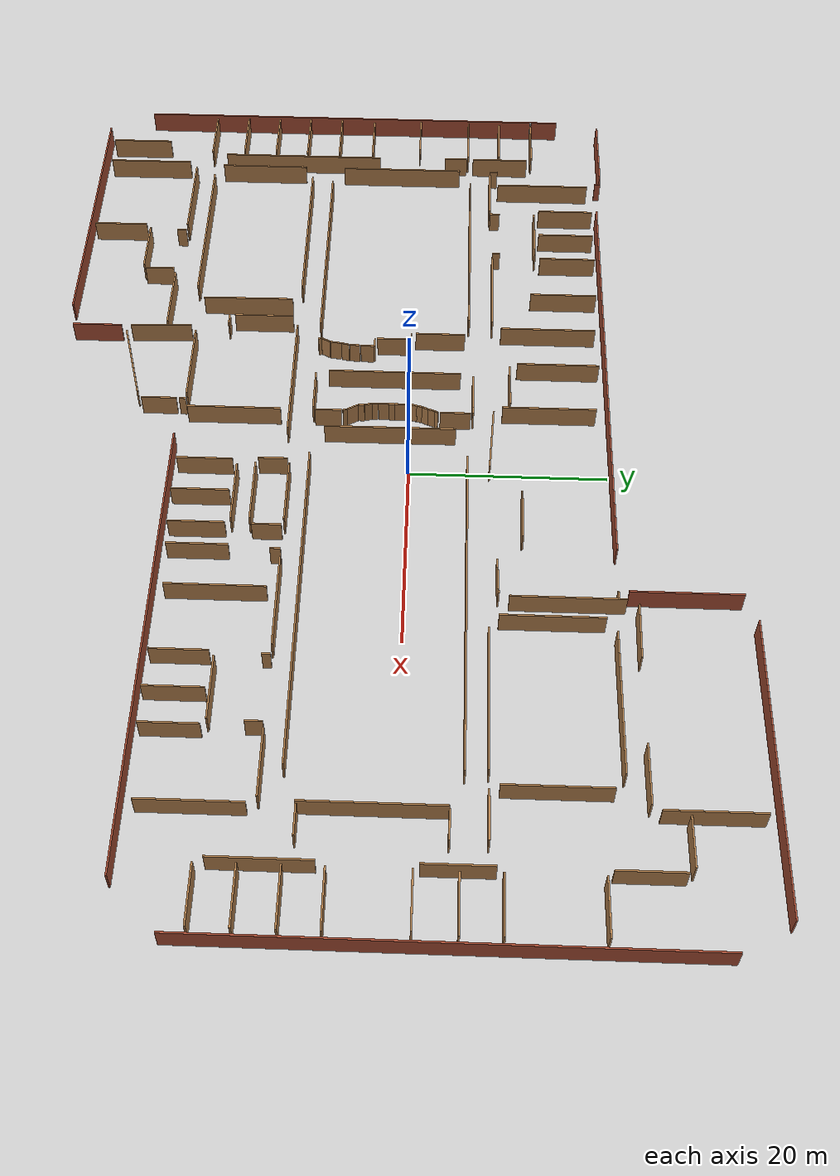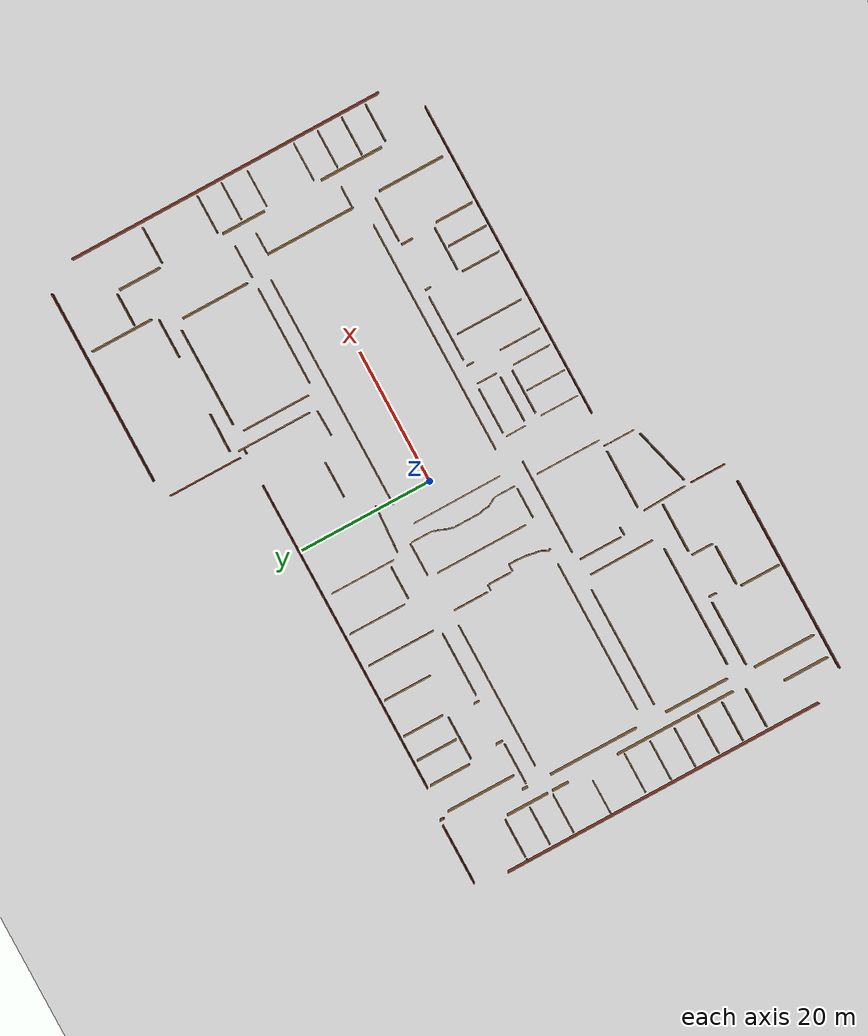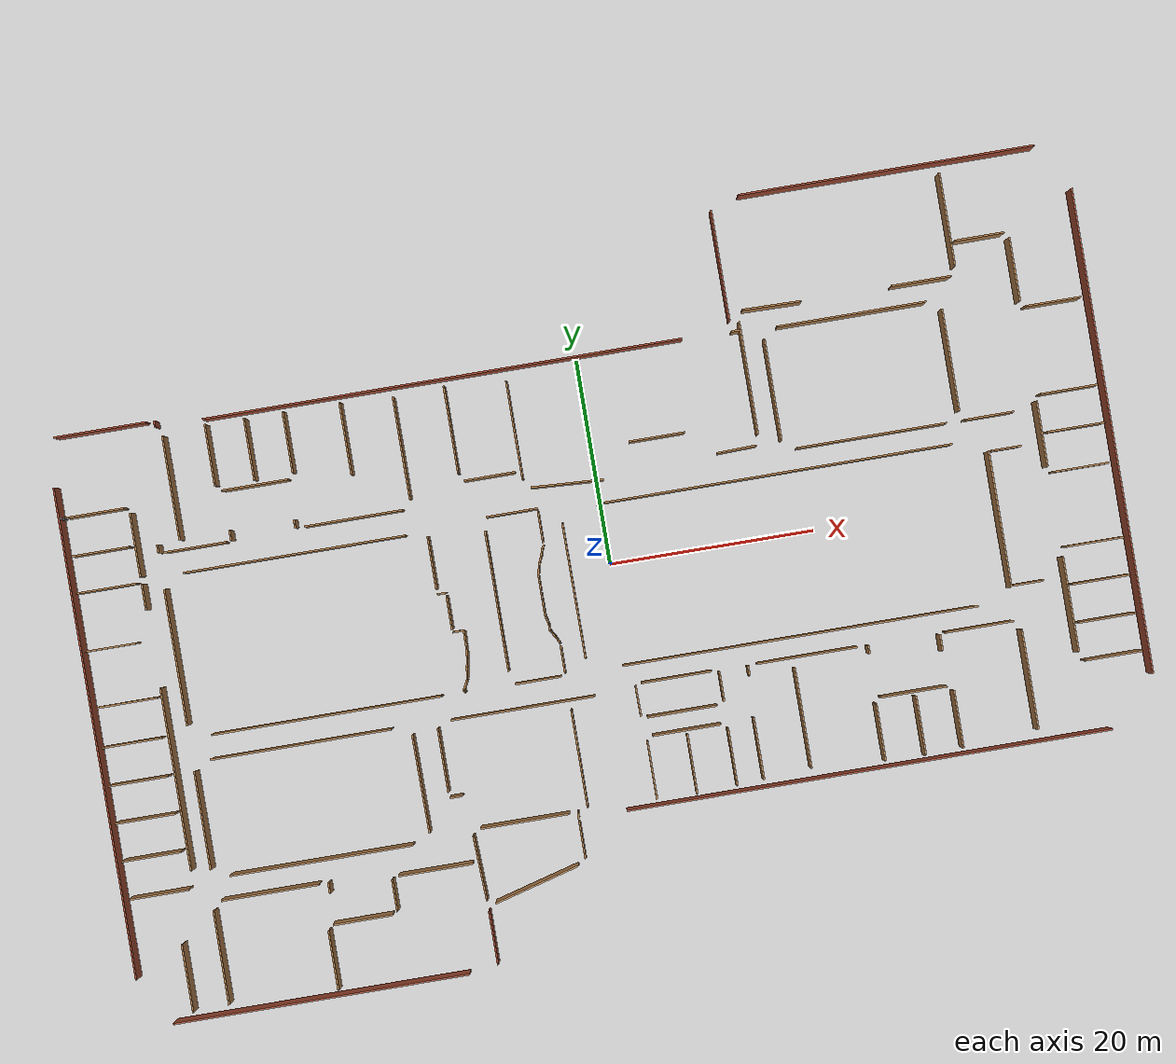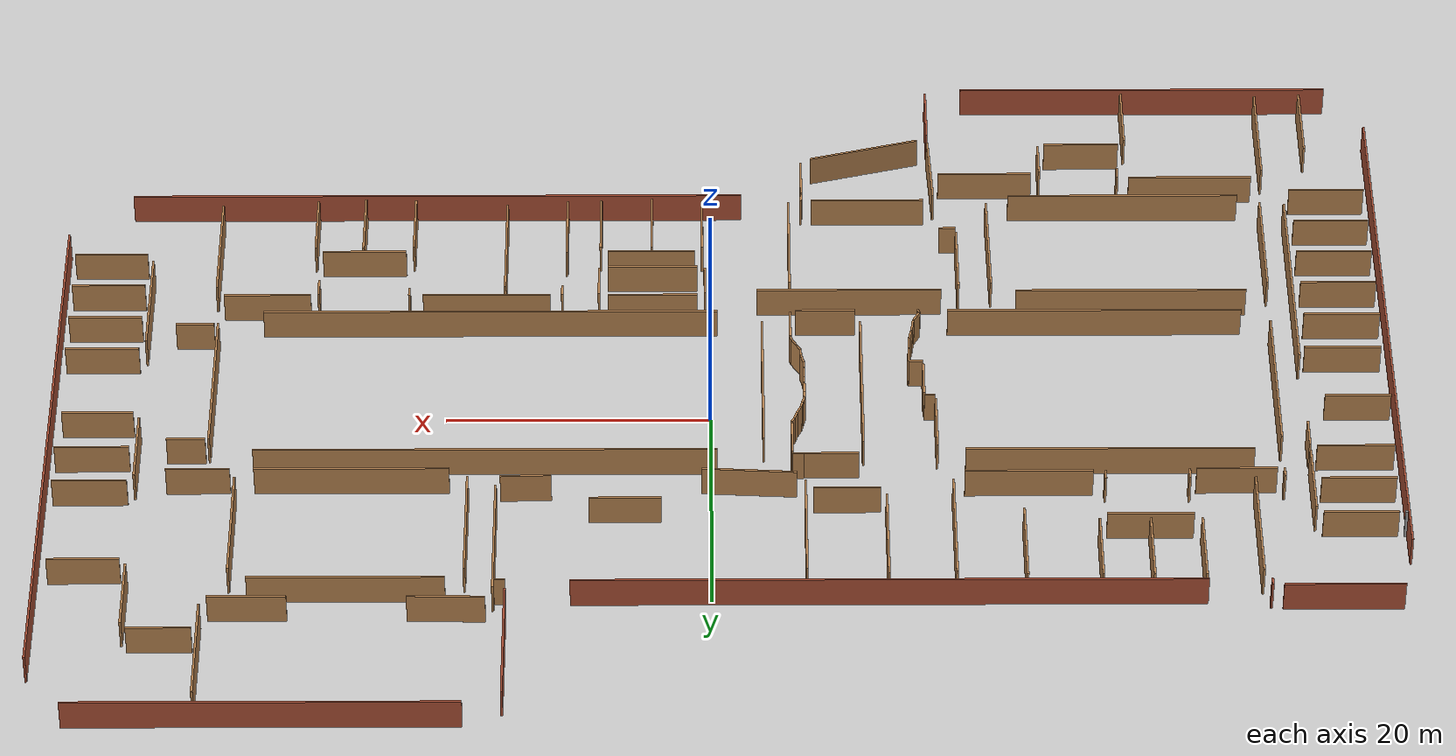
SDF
<sdf version="1.6">
 <world name="default">
  <light name="sun" type="directional">
   <pose>0 0 10 0 -0 0</pose>
   <diffuse>0.8 0.8 0.8 1</diffuse>
   <specular>0.2 0.2 0.2 1</specular>
   <attenuation>
    <range>1000</range>
    <constant>0.9</constant>
    <linear>0.01</linear>
    <quadratic>0.001</quadratic>
   </attenuation>
   <direction>-0.5 0.1 -0.9</direction>
  </light>
  <model name="ground_plane">
   <static>1</static>
   <link name="link">
    <collision name="collision">
     <geometry><plane><normal>0 0 1</normal><size>100 100</size></plane></geometry>
     <surface><friction><ode><mu>100</mu><mu2>50</mu2></ode></friction></surface>
    </collision>
    <visual name="visual">
     <cast_shadows>0</cast_shadows>
     <geometry><plane><normal>0 0 1</normal><size>100 100</size></plane></geometry>
     <material>
      <ambient>1.0 1.0 1.0 1.0</ambient>
      <diffuse>0.8 0.8 0.8 1.0</diffuse>
      <specular>0.01 0.01 0.01 1.000000</specular>
     </material>
    </visual>
   </link>
  </model>
  <gravity>0 0 -9.8</gravity>
  <magnetic_field>6e-06 2.3e-05 -4.2e-05</magnetic_field>
  <atmosphere type="adiabatic"/>
  <physics default="0" name="default_physics" type="ode">
   <max_step_size>0.001</max_step_size>
   <real_time_factor>1</real_time_factor>
   <real_time_update_rate>1000</real_time_update_rate>
  </physics>
  <scene><ambient>0.4 0.4 0.4 1</ambient><background>0.7 0.7 0.7 1</background><shadows>1</shadows></scene>
  <spherical_coordinates>
   <surface_model>EARTH_WGS84</surface_model>
   <latitude_deg>0</latitude_deg>
   <longitude_deg>0</longitude_deg>
   <elevation>0</elevation>
   <heading_deg>0</heading_deg>
  </spherical_coordinates>
  <model name="NamedLocations">
   <static>true</static>
   <link name="DefaultStart"><pose>38 -1.7 0 0 0 3.14</pose></link>
  </model>
  <model name="HighNamedLocations">
   <static>true</static>
   <link name="HighDefaultStart"><pose>38 -1.7 0.65 0 0 3.14</pose></link>
  </model>
  <model name="floorPlan">
   <pose>-1.03517 -1.87284 0 0 -0 0</pose>
   <link name="Wall_101">
    <collision name="Wall_101_Collision">
     <geometry><box><size>8.95 0.15 2.50</size></box></geometry>
     <pose>0 0 1.25 0 -0 0</pose>
    </collision>
    <visual name="Wall_101_Visual">
     <pose>0 0 1.25 0 -0 0</pose>
     <geometry><box><size>8.95 0.15 2.50</size></box></geometry>
     <material>
      <script><uri>file://media/materials/scripts/gazebo.material</uri><name>Gazebo/Bricks</name></script>
      <ambient>1 1 1 1</ambient>
     </material>
     <meta><layer>0</layer></meta>
    </visual>
    <pose>-45.3755 22.7356 0 0 -0 0</pose>
   </link>
   <link name="Wall_102">
    <collision name="Wall_102_Collision">
     <geometry><box><size>0.62 0.15 2.50</size></box></geometry>
     <pose>0 0 1.25 0 -0 0</pose>
    </collision>
    <visual name="Wall_102_Visual">
     <pose>0 0 1.25 0 -0 0</pose>
     <geometry><box><size>0.62 0.15 2.50</size></box></geometry>
     <material>
      <script><uri>file://media/materials/scripts/gazebo.material</uri><name>Gazebo/Bricks</name></script>
      <ambient>1 1 1 1</ambient>
     </material>
     <meta><layer>0</layer></meta>
    </visual>
    <pose>-40.0755 22.4356 0 0 0 -1.5708</pose>
   </link>
   <link name="Wall_103">
    <collision name="Wall_103_Collision">
     <geometry><box><size>46.86 0.15 2.50</size></box></geometry>
     <pose>0 0 1.25 0 -0 0</pose>
    </collision>
    <visual name="Wall_103_Visual">
     <pose>0 0 1.25 0 -0 0</pose>
     <geometry><box><size>46.86 0.15 2.50</size></box></geometry>
     <material>
      <script><uri>file://media/materials/scripts/gazebo.material</uri><name>Gazebo/Bricks</name></script>
      <ambient>1 1 1 1</ambient>
     </material>
     <meta><layer>0</layer></meta>
    </visual>
    <pose>-12.0255 22.1356 0 0 -0 0</pose>
   </link>
   <link name="Wall_105">
    <collision name="Wall_105_Collision">
     <geometry><box><size>10.83 0.15 2.50</size></box></geometry>
     <pose>0 0 1.25 0 -0 0</pose>
    </collision>
    <visual name="Wall_105_Visual">
     <pose>0 0 1.25 0 -0 0</pose>
     <geometry><box><size>10.83 0.15 2.50</size></box></geometry>
     <material>
      <script><uri>file://media/materials/scripts/gazebo.material</uri><name>Gazebo/Bricks</name></script>
      <ambient>1 1 1 1</ambient>
     </material>
     <meta><layer>0</layer></meta>
    </visual>
    <pose>16.1718 28.4394 0 0 0 -1.5708</pose>
   </link>
   <link name="Wall_107">
    <collision name="Wall_107_Collision">
     <geometry><box><size>0.83 0.15 2.50</size></box></geometry>
     <pose>0 0 1.25 0 -0 0</pose>
    </collision>
    <visual name="Wall_107_Visual">
     <pose>0 0 1.25 0 -0 0</pose>
     <geometry><box><size>0.83 0.15 2.50</size></box></geometry>
     <material>
      <script><uri>file://media/materials/scripts/gazebo.material</uri><name>Gazebo/Wood</name></script>
      <ambient>1 1 1 1</ambient>
     </material>
     <meta><layer>0</layer></meta>
    </visual>
    <pose>16.5968 22.0144 0 0 -0 0</pose>
   </link>
   <link name="Wall_109">
    <collision name="Wall_109_Collision">
     <geometry><box><size>9.79 0.15 2.50</size></box></geometry>
     <pose>0 0 1.25 0 -0 0</pose>
    </collision>
    <visual name="Wall_109_Visual">
     <pose>0 0 1.25 0 -0 0</pose>
     <geometry><box><size>9.79 0.15 2.50</size></box></geometry>
     <material>
      <script><uri>file://media/materials/scripts/gazebo.material</uri><name>Gazebo/Wood</name></script>
      <ambient>1 1 1 1</ambient>
     </material>
     <meta><layer>0</layer></meta>
    </visual>
    <pose>39.004 -15.7975 0 0 0 -1.5708</pose>
   </link>
   <link name="Wall_111">
    <collision name="Wall_111_Collision">
     <geometry><box><size>6.66 0.15 2.50</size></box></geometry>
     <pose>0 0 1.25 0 -0 0</pose>
    </collision>
    <visual name="Wall_111_Visual">
     <pose>0 0 1.25 0 -0 0</pose>
     <geometry><box><size>6.66 0.15 2.50</size></box></geometry>
     <material>
      <script><uri>file://media/materials/scripts/gazebo.material</uri><name>Gazebo/Wood</name></script>
      <ambient>1 1 1 1</ambient>
     </material>
     <meta><layer>0</layer></meta>
    </visual>
    <pose>35.079 -9.99746 0 0 -0 3.14159</pose>
   </link>
   <link name="Wall_112">
    <collision name="Wall_112_Collision">
     <geometry><box><size>1.67 0.15 2.50</size></box></geometry>
     <pose>0 0 1.25 0 -0 0</pose>
    </collision>
    <visual name="Wall_112_Visual">
     <pose>0 0 1.25 0 -0 0</pose>
     <geometry><box><size>1.67 0.15 2.50</size></box></geometry>
     <material>
      <script><uri>file://media/materials/scripts/gazebo.material</uri><name>Gazebo/Wood</name></script>
      <ambient>1 1 1 1</ambient>
     </material>
     <meta><layer>0</layer></meta>
    </visual>
    <pose>31.154 -10.9225 0 0 0 -1.5708</pose>
   </link>
   <link name="Wall_114">
    <collision name="Wall_114_Collision">
     <geometry><box><size>5.62 0.15 2.50</size></box></geometry>
     <pose>0 0 1.25 0 -0 0</pose>
    </collision>
    <visual name="Wall_114_Visual">
     <pose>0 0 1.25 0 -0 0</pose>
     <geometry><box><size>5.62 0.15 2.50</size></box></geometry>
     <material>
      <script><uri>file://media/materials/scripts/gazebo.material</uri><name>Gazebo/Wood</name></script>
      <ambient>1 1 1 1</ambient>
     </material>
     <meta><layer>0</layer></meta>
    </visual>
    <pose>31.5938 -18.4328 0 0 -0 1.5708</pose>
   </link>
   <link name="Wall_115">
    <collision name="Wall_115_Collision">
     <geometry><box><size>6.46 0.15 2.50</size></box></geometry>
     <pose>0 0 1.25 0 -0 0</pose>
    </collision>
    <visual name="Wall_115_Visual">
     <pose>0 0 1.25 0 -0 0</pose>
     <geometry><box><size>6.46 0.15 2.50</size></box></geometry>
     <material>
      <script><uri>file://media/materials/scripts/gazebo.material</uri><name>Gazebo/Wood</name></script>
      <ambient>1 1 1 1</ambient>
     </material>
     <meta><layer>0</layer></meta>
    </visual>
    <pose>27.7938 -15.1328 0 0 -0 3.14159</pose>
   </link>
   <link name="Wall_116">
    <collision name="Wall_116_Collision">
     <geometry><box><size>5.62 0.15 2.50</size></box></geometry>
     <pose>0 0 1.25 0 -0 0</pose>
    </collision>
    <visual name="Wall_116_Visual">
     <pose>0 0 1.25 0 -0 0</pose>
     <geometry><box><size>5.62 0.15 2.50</size></box></geometry>
     <material>
      <script><uri>file://media/materials/scripts/gazebo.material</uri><name>Gazebo/Wood</name></script>
      <ambient>1 1 1 1</ambient>
     </material>
     <meta><layer>0</layer></meta>
    </visual>
    <pose>23.9938 -18.4328 0 0 0 -1.5708</pose>
   </link>
   <link name="Wall_118">
    <collision name="Wall_118_Collision">
     <geometry><box><size>0.83 0.15 2.50</size></box></geometry>
     <pose>0 0 1.25 0 -0 0</pose>
    </collision>
    <visual name="Wall_118_Visual">
     <pose>0 0 1.25 0 -0 0</pose>
     <geometry><box><size>0.83 0.15 2.50</size></box></geometry>
     <material>
      <script><uri>file://media/materials/scripts/gazebo.material</uri><name>Gazebo/Wood</name></script>
      <ambient>1 1 1 1</ambient>
     </material>
     <meta><layer>0</layer></meta>
    </visual>
    <pose>24.1778 -10.3922 0 0 0 -1.5708</pose>
   </link>
   <link name="Wall_120">
    <collision name="Wall_120_Collision">
     <geometry><box><size>9.79 0.15 2.50</size></box></geometry>
     <pose>0 0 1.25 0 -0 0</pose>
    </collision>
    <visual name="Wall_120_Visual">
     <pose>0 0 1.25 0 -0 0</pose>
     <geometry><box><size>9.79 0.15 2.50</size></box></geometry>
     <material>
      <script><uri>file://media/materials/scripts/gazebo.material</uri><name>Gazebo/Wood</name></script>
      <ambient>1 1 1 1</ambient>
     </material>
     <meta><layer>0</layer></meta>
    </visual>
    <pose>18.2324 -9.96721 0 0 -0 3.14159</pose>
   </link>
   <link name="Wall_121">
    <collision name="Wall_121_Collision">
     <geometry><box><size>1.04 0.15 2.50</size></box></geometry>
     <pose>0 0 1.25 0 -0 0</pose>
    </collision>
    <visual name="Wall_121_Visual">
     <pose>0 0 1.25 0 -0 0</pose>
     <geometry><box><size>1.04 0.15 2.50</size></box></geometry>
     <material>
      <script><uri>file://media/materials/scripts/gazebo.material</uri><name>Gazebo/Wood</name></script>
      <ambient>1 1 1 1</ambient>
     </material>
     <meta><layer>0</layer></meta>
    </visual>
    <pose>12.4324 -10.5172 0 0 0 -1.5708</pose>
   </link>
   <link name="Wall_123">
    <collision name="Wall_123_Collision">
     <geometry><box><size>9.79 0.15 2.50</size></box></geometry>
     <pose>0 0 1.25 0 -0 0</pose>
    </collision>
    <visual name="Wall_123_Visual">
     <pose>0 0 1.25 0 -0 0</pose>
     <geometry><box><size>9.79 0.15 2.50</size></box></geometry>
     <material>
      <script><uri>file://media/materials/scripts/gazebo.material</uri><name>Gazebo/Wood</name></script>
      <ambient>1 1 1 1</ambient>
     </material>
     <meta><layer>0</layer></meta>
    </visual>
    <pose>16.8339 -15.8579 0 0 0 -1.5708</pose>
   </link>
   <link name="Wall_125">
    <collision name="Wall_125_Collision">
     <geometry><box><size>6.04 0.15 2.50</size></box></geometry>
     <pose>0 0 1.25 0 -0 0</pose>
    </collision>
    <visual name="Wall_125_Visual">
     <pose>0 0 1.25 0 -0 0</pose>
     <geometry><box><size>6.04 0.15 2.50</size></box></geometry>
     <material>
      <script><uri>file://media/materials/scripts/gazebo.material</uri><name>Gazebo/Wood</name></script>
      <ambient>1 1 1 1</ambient>
     </material>
     <meta><layer>0</layer></meta>
    </visual>
    <pose>12.1458 -18.0541 0 0 0 -1.5708</pose>
   </link>
   <link name="Wall_127">
    <collision name="Wall_127_Collision">
     <geometry><box><size>9.58 0.15 2.50</size></box></geometry>
     <pose>0 0 1.25 0 -0 0</pose>
    </collision>
    <visual name="Wall_127_Visual">
     <pose>0 0 1.25 0 -0 0</pose>
     <geometry><box><size>9.58 0.15 2.50</size></box></geometry>
     <material>
      <script><uri>file://media/materials/scripts/gazebo.material</uri><name>Gazebo/Wood</name></script>
      <ambient>1 1 1 1</ambient>
     </material>
     <meta><layer>0</layer></meta>
    </visual>
    <pose>-5.05877 -16.1593 0 0 0 -1.5708</pose>
   </link>
   <link name="Wall_129">
    <collision name="Wall_129_Collision">
     <geometry><box><size>14.16 0.15 2.50</size></box></geometry>
     <pose>0 0 1.25 0 -0 0</pose>
    </collision>
    <visual name="Wall_129_Visual">
     <pose>0 0 1.25 0 -0 0</pose>
     <geometry><box><size>14.16 0.15 2.50</size></box></geometry>
     <material>
      <script><uri>file://media/materials/scripts/gazebo.material</uri><name>Gazebo/Wood</name></script>
      <ambient>1 1 1 1</ambient>
     </material>
     <meta><layer>0</layer></meta>
    </visual>
    <pose>-9.61757 -10.458 0 0 -0 3.14159</pose>
   </link>
   <link name="Wall_130">
    <collision name="Wall_130_Collision">
     <geometry><box><size>6.25 0.15 2.50</size></box></geometry>
     <pose>0 0 1.25 0 -0 0</pose>
    </collision>
    <visual name="Wall_130_Visual">
     <pose>0 0 1.25 0 -0 0</pose>
     <geometry><box><size>6.25 0.15 2.50</size></box></geometry>
     <material>
      <script><uri>file://media/materials/scripts/gazebo.material</uri><name>Gazebo/Wood</name></script>
      <ambient>1 1 1 1</ambient>
     </material>
     <meta><layer>0</layer></meta>
    </visual>
    <pose>-18.0426 -14.133 0 0 0 -1.5708</pose>
   </link>
   <link name="Wall_131">
    <collision name="Wall_131_Collision">
     <geometry><box><size>1.25 0.15 2.50</size></box></geometry>
     <pose>0 0 1.25 0 -0 0</pose>
    </collision>
    <visual name="Wall_131_Visual">
     <pose>0 0 1.25 0 -0 0</pose>
     <geometry><box><size>1.25 0.15 2.50</size></box></geometry>
     <material>
      <script><uri>file://media/materials/scripts/gazebo.material</uri><name>Gazebo/Wood</name></script>
      <ambient>1 1 1 1</ambient>
     </material>
     <meta><layer>0</layer></meta>
    </visual>
    <pose>-17.3676 -17.808 0 0 -0 0</pose>
   </link>
   <link name="Wall_133">
    <collision name="Wall_133_Collision">
     <geometry><box><size>8.75 0.15 2.50</size></box></geometry>
     <pose>0 0 1.25 0 -0 0</pose>
    </collision>
    <visual name="Wall_133_Visual">
     <pose>0 0 1.25 0 -0 0</pose>
     <geometry><box><size>8.75 0.15 2.50</size></box></geometry>
     <material>
      <script><uri>file://media/materials/scripts/gazebo.material</uri><name>Gazebo/Wood</name></script>
      <ambient>1 1 1 1</ambient>
     </material>
     <meta><layer>0</layer></meta>
    </visual>
    <pose>-11.2193 -21.215 0 0 -0 0</pose>
   </link>
   <link name="Wall_134">
    <collision name="Wall_134_Collision">
     <geometry><box><size>0.69 0.15 2.50</size></box></geometry>
     <pose>0 0 1.25 0 -0 0</pose>
    </collision>
    <visual name="Wall_134_Visual">
     <pose>0 0 1.25 0 -0 0</pose>
     <geometry><box><size>0.69 0.15 2.50</size></box></geometry>
     <material>
      <script><uri>file://media/materials/scripts/gazebo.material</uri><name>Gazebo/Wood</name></script>
      <ambient>1 1 1 1</ambient>
     </material>
     <meta><layer>0</layer></meta>
    </visual>
    <pose>-6.06127 -21.5509 0 0 0 -1.62113</pose>
   </link>
   <link name="Wall_137">
    <collision name="Wall_137_Collision">
     <geometry><box><size>6.42 0.15 2.50</size></box></geometry>
     <pose>0 0 1.25 0 -0 0</pose>
    </collision>
    <visual name="Wall_137_Visual">
     <pose>0 0 1.25 0 -0 0</pose>
     <geometry><box><size>6.42 0.15 2.50</size></box></geometry>
     <material>
      <script><uri>file://media/materials/scripts/gazebo.material</uri><name>Gazebo/Wood</name></script>
      <ambient>1 1 1 1</ambient>
     </material>
     <meta><layer>0</layer></meta>
    </visual>
    <pose>-16.2349 -24.9897 0 0 0 -1.52859</pose>
   </link>
   <link name="Wall_139">
    <collision name="Wall_139_Collision">
     <geometry><box><size>7.29 0.15 2.50</size></box></geometry>
     <pose>0 0 1.25 0 -0 0</pose>
    </collision>
    <visual name="Wall_139_Visual">
     <pose>0 0 1.25 0 -0 0</pose>
     <geometry><box><size>7.29 0.15 2.50</size></box></geometry>
     <material>
      <script><uri>file://media/materials/scripts/gazebo.material</uri><name>Gazebo/Wood</name></script>
      <ambient>1 1 1 1</ambient>
     </material>
     <meta><layer>0</layer></meta>
    </visual>
    <pose>-20.4877 -24.4086 0 0 -0 3.14159</pose>
   </link>
   <link name="Wall_140">
    <collision name="Wall_140_Collision">
     <geometry><box><size>3.12 0.15 2.50</size></box></geometry>
     <pose>0 0 1.25 0 -0 0</pose>
    </collision>
    <visual name="Wall_140_Visual">
     <pose>0 0 1.25 0 -0 0</pose>
     <geometry><box><size>3.12 0.15 2.50</size></box></geometry>
     <material>
      <script><uri>file://media/materials/scripts/gazebo.material</uri><name>Gazebo/Wood</name></script>
      <ambient>1 1 1 1</ambient>
     </material>
     <meta><layer>0</layer></meta>
    </visual>
    <pose>-24.7877 -26.2086 0 0 0 -1.5708</pose>
   </link>
   <link name="Wall_141">
    <collision name="Wall_141_Collision">
     <geometry><box><size>5.83 0.15 2.50</size></box></geometry>
     <pose>0 0 1.25 0 -0 0</pose>
    </collision>
    <visual name="Wall_141_Visual">
     <pose>0 0 1.25 0 -0 0</pose>
     <geometry><box><size>5.83 0.15 2.50</size></box></geometry>
     <material>
      <script><uri>file://media/materials/scripts/gazebo.material</uri><name>Gazebo/Wood</name></script>
      <ambient>1 1 1 1</ambient>
     </material>
     <meta><layer>0</layer></meta>
    </visual>
    <pose>-28.2127 -28.0086 0 0 -0 3.14159</pose>
   </link>
   <link name="Wall_142">
    <collision name="Wall_142_Collision">
     <geometry><box><size>5.83 0.15 2.50</size></box></geometry>
     <pose>0 0 1.25 0 -0 0</pose>
    </collision>
    <visual name="Wall_142_Visual">
     <pose>0 0 1.25 0 -0 0</pose>
     <geometry><box><size>5.83 0.15 2.50</size></box></geometry>
     <material>
      <script><uri>file://media/materials/scripts/gazebo.material</uri><name>Gazebo/Wood</name></script>
      <ambient>1 1 1 1</ambient>
     </material>
     <meta><layer>0</layer></meta>
    </visual>
    <pose>-31.6377 -31.4336 0 0 0 -1.5708</pose>
   </link>
   <link name="Wall_144">
    <collision name="Wall_144_Collision">
     <geometry><box><size>1.04 0.15 2.50</size></box></geometry>
     <pose>0 0 1.25 0 -0 0</pose>
    </collision>
    <visual name="Wall_144_Visual">
     <pose>0 0 1.25 0 -0 0</pose>
     <geometry><box><size>1.04 0.15 2.50</size></box></geometry>
     <material>
      <script><uri>file://media/materials/scripts/gazebo.material</uri><name>Gazebo/Wood</name></script>
      <ambient>1 1 1 1</ambient>
     </material>
     <meta><layer>0</layer></meta>
    </visual>
    <pose>-30.9008 -24.4847 0 0 -0 1.5708</pose>
   </link>
   <link name="Wall_146">
    <collision name="Wall_146_Collision">
     <geometry><box><size>9.58 0.15 2.50</size></box></geometry>
     <pose>0 0 1.25 0 -0 0</pose>
    </collision>
    <visual name="Wall_146_Visual">
     <pose>0 0 1.25 0 -0 0</pose>
     <geometry><box><size>9.58 0.15 2.50</size></box></geometry>
     <material>
      <script><uri>file://media/materials/scripts/gazebo.material</uri><name>Gazebo/Wood</name></script>
      <ambient>1 1 1 1</ambient>
     </material>
     <meta><layer>0</layer></meta>
    </visual>
    <pose>-36.5758 -23.9347 0 0 -0 3.14159</pose>
   </link>
   <link name="Wall_147">
    <collision name="Wall_147_Collision">
     <geometry><box><size>9.16 0.15 2.50</size></box></geometry>
     <pose>0 0 1.25 0 -0 0</pose>
    </collision>
    <visual name="Wall_147_Visual">
     <pose>0 0 1.25 0 -0 0</pose>
     <geometry><box><size>9.16 0.15 2.50</size></box></geometry>
     <material>
      <script><uri>file://media/materials/scripts/gazebo.material</uri><name>Gazebo/Wood</name></script>
      <ambient>1 1 1 1</ambient>
     </material>
     <meta><layer>0</layer></meta>
    </visual>
    <pose>-42.2508 -29.3597 0 0 0 -1.5708</pose>
   </link>
   <link name="Wall_149">
    <collision name="Wall_149_Collision">
     <geometry><box><size>6.66 0.15 2.50</size></box></geometry>
     <pose>0 0 1.25 0 -0 0</pose>
    </collision>
    <visual name="Wall_149_Visual">
     <pose>0 0 1.25 0 -0 0</pose>
     <geometry><box><size>6.66 0.15 2.50</size></box></geometry>
     <material>
      <script><uri>file://media/materials/scripts/gazebo.material</uri><name>Gazebo/Wood</name></script>
      <ambient>1 1 1 1</ambient>
     </material>
     <meta><layer>0</layer></meta>
    </visual>
    <pose>-45.7877 -30.8032 0 0 0 -1.5708</pose>
   </link>
   <link name="Wall_151">
    <collision name="Wall_151_Collision">
     <geometry><box><size>5.83 0.15 2.50</size></box></geometry>
     <pose>0 0 1.25 0 -0 0</pose>
    </collision>
    <visual name="Wall_151_Visual">
     <pose>0 0 1.25 0 -0 0</pose>
     <geometry><box><size>5.83 0.15 2.50</size></box></geometry>
     <material>
      <script><uri>file://media/materials/scripts/gazebo.material</uri><name>Gazebo/Wood</name></script>
      <ambient>1 1 1 1</ambient>
     </material>
     <meta><layer>0</layer></meta>
    </visual>
    <pose>-47.1627 -22.3564 0 0 -0 0</pose>
   </link>
   <link name="Wall_152">
    <collision name="Wall_152_Collision">
     <geometry><box><size>17.91 0.15 2.50</size></box></geometry>
     <pose>0 0 1.25 0 -0 0</pose>
    </collision>
    <visual name="Wall_152_Visual">
     <pose>0 0 1.25 0 -0 0</pose>
     <geometry><box><size>17.91 0.15 2.50</size></box></geometry>
     <material>
      <script><uri>file://media/materials/scripts/gazebo.material</uri><name>Gazebo/Wood</name></script>
      <ambient>1 1 1 1</ambient>
     </material>
     <meta><layer>0</layer></meta>
    </visual>
    <pose>-43.7377 -11.6814 0 0 -0 1.5708</pose>
   </link>
   <link name="Wall_154">
    <collision name="Wall_154_Collision">
     <geometry><box><size>9.58 0.15 2.50</size></box></geometry>
     <pose>0 0 1.25 0 -0 0</pose>
    </collision>
    <visual name="Wall_154_Visual">
     <pose>0 0 1.25 0 -0 0</pose>
     <geometry><box><size>9.58 0.15 2.50</size></box></geometry>
     <material>
      <script><uri>file://media/materials/scripts/gazebo.material</uri><name>Gazebo/Wood</name></script>
      <ambient>1 1 1 1</ambient>
     </material>
     <meta><layer>0</layer></meta>
    </visual>
    <pose>-20.5182 -16.0314 0 0 0 -1.5616</pose>
   </link>
   <link name="Wall_155">
    <collision name="Wall_155_Collision">
     <geometry><box><size>17.91 0.15 2.50</size></box></geometry>
     <pose>0 0 1.25 0 -0 0</pose>
    </collision>
    <visual name="Wall_155_Visual">
     <pose>0 0 1.25 0 -0 0</pose>
     <geometry><box><size>17.91 0.15 2.50</size></box></geometry>
     <material>
      <script><uri>file://media/materials/scripts/gazebo.material</uri><name>Gazebo/Wood</name></script>
      <ambient>1 1 1 1</ambient>
     </material>
     <meta><layer>0</layer></meta>
    </visual>
    <pose>-31.1758 -21.7064 0 0 -0 3.14159</pose>
   </link>
   <link name="Wall_158">
    <collision name="Wall_158_Collision">
     <geometry><box><size>9.58 0.15 2.50</size></box></geometry>
     <pose>0 0 1.25 0 -0 0</pose>
    </collision>
    <visual name="Wall_158_Visual">
     <pose>0 0 1.25 0 -0 0</pose>
     <geometry><box><size>9.58 0.15 2.50</size></box></geometry>
     <material>
      <script><uri>file://media/materials/scripts/gazebo.material</uri><name>Gazebo/Wood</name></script>
      <ambient>1 1 1 1</ambient>
     </material>
     <meta><layer>0</layer></meta>
    </visual>
    <pose>-41.8508 -16.0314 0 0 -0 1.5708</pose>
   </link>
   <link name="Wall_159">
    <collision name="Wall_159_Collision">
     <geometry><box><size>17.70 0.15 2.50</size></box></geometry>
     <pose>0 0 1.25 0 -0 0</pose>
    </collision>
    <visual name="Wall_159_Visual">
     <pose>0 0 1.25 0 -0 0</pose>
     <geometry><box><size>17.70 0.15 2.50</size></box></geometry>
     <material>
      <script><uri>file://media/materials/scripts/gazebo.material</uri><name>Gazebo/Wood</name></script>
      <ambient>1 1 1 1</ambient>
     </material>
     <meta><layer>0</layer></meta>
    </visual>
    <pose>-31.3008 -10.3564 0 0 -0 0</pose>
   </link>
   <link name="Wall_161">
    <collision name="Wall_161_Collision">
     <geometry><box><size>4.17 0.15 2.50</size></box></geometry>
     <pose>0 0 1.25 0 -0 0</pose>
    </collision>
    <visual name="Wall_161_Visual">
     <pose>0 0 1.25 0 -0 0</pose>
     <geometry><box><size>4.17 0.15 2.50</size></box></geometry>
     <material>
      <script><uri>file://media/materials/scripts/gazebo.material</uri><name>Gazebo/Wood</name></script>
      <ambient>1 1 1 1</ambient>
     </material>
     <meta><layer>0</layer></meta>
    </visual>
    <pose>-7.97942 8.30014 0 0 -0 3.14159</pose>
   </link>
   <link name="Wall_162">
    <collision name="Wall_162_Collision">
     <geometry><box><size>13.74 0.15 2.50</size></box></geometry>
     <pose>0 0 1.25 0 -0 0</pose>
    </collision>
    <visual name="Wall_162_Visual">
     <pose>0 0 1.25 0 -0 0</pose>
     <geometry><box><size>13.74 0.15 2.50</size></box></geometry>
     <material>
      <script><uri>file://media/materials/scripts/gazebo.material</uri><name>Gazebo/Wood</name></script>
      <ambient>1 1 1 1</ambient>
     </material>
     <meta><layer>0</layer></meta>
    </visual>
    <pose>-10.4044 0.125141 0 0 0 -1.5708</pose>
   </link>
   <link name="Wall_163">
    <collision name="Wall_163_Collision">
     <geometry><box><size>4.58 0.15 2.50</size></box></geometry>
     <pose>0 0 1.25 0 -0 0</pose>
    </collision>
    <visual name="Wall_163_Visual">
     <pose>0 0 1.25 0 -0 0</pose>
     <geometry><box><size>4.58 0.15 2.50</size></box></geometry>
     <material>
      <script><uri>file://media/materials/scripts/gazebo.material</uri><name>Gazebo/Wood</name></script>
      <ambient>1 1 1 1</ambient>
     </material>
     <meta><layer>0</layer></meta>
    </visual>
    <pose>-7.72942 -8.04986 0 0 -0 0</pose>
   </link>
   <link name="Wall_164">
    <collision name="Wall_164_Collision">
     <geometry><box><size>2.71 0.15 2.50</size></box></geometry>
     <pose>0 0 1.25 0 -0 0</pose>
    </collision>
    <visual name="Wall_164_Visual">
     <pose>0 0 1.25 0 -0 0</pose>
     <geometry><box><size>2.71 0.15 2.50</size></box></geometry>
     <material>
      <script><uri>file://media/materials/scripts/gazebo.material</uri><name>Gazebo/Wood</name></script>
      <ambient>1 1 1 1</ambient>
     </material>
     <meta><layer>0</layer></meta>
    </visual>
    <pose>-5.05442 -6.49986 0 0 -0 1.5708</pose>
   </link>
   <link name="Wall_165">
    <collision name="Wall_165_Collision">
     <geometry><box><size>0.42 0.15 2.50</size></box></geometry>
     <pose>0 0 1.25 0 -0 0</pose>
    </collision>
    <visual name="Wall_165_Visual">
     <pose>0 0 1.25 0 -0 0</pose>
     <geometry><box><size>0.42 0.15 2.50</size></box></geometry>
     <material>
      <script><uri>file://media/materials/scripts/gazebo.material</uri><name>Gazebo/Wood</name></script>
      <ambient>1 1 1 1</ambient>
     </material>
     <meta><layer>0</layer></meta>
    </visual>
    <pose>-5.09971 -4.78082 0 0 -0 1.8326</pose>
   </link>
   <link name="Wall_166">
    <collision name="Wall_166_Collision">
     <geometry><box><size>1.25 0.15 2.50</size></box></geometry>
     <pose>0 0 1.25 0 -0 0</pose>
    </collision>
    <visual name="Wall_166_Visual">
     <pose>0 0 1.25 0 -0 0</pose>
     <geometry><box><size>1.25 0.15 2.50</size></box></geometry>
     <material>
      <script><uri>file://media/materials/scripts/gazebo.material</uri><name>Gazebo/Wood</name></script>
      <ambient>1 1 1 1</ambient>
     </material>
     <meta><layer>0</layer></meta>
    </visual>
    <pose>-5.4825 -4.02722 0 0 -0 2.0944</pose>
   </link>
   <link name="Wall_167">
    <collision name="Wall_167_Collision">
     <geometry><box><size>0.62 0.15 2.50</size></box></geometry>
     <pose>0 0 1.25 0 -0 0</pose>
    </collision>
    <visual name="Wall_167_Visual">
     <pose>0 0 1.25 0 -0 0</pose>
     <geometry><box><size>0.62 0.15 2.50</size></box></geometry>
     <material>
      <script><uri>file://media/materials/scripts/gazebo.material</uri><name>Gazebo/Wood</name></script>
      <ambient>1 1 1 1</ambient>
     </material>
     <meta><layer>0</layer></meta>
    </visual>
    <pose>-5.82 -3.14265 0 0 -0 1.5708</pose>
   </link>
   <link name="Wall_168">
    <collision name="Wall_168_Collision">
     <geometry><box><size>0.83 0.15 2.50</size></box></geometry>
     <pose>0 0 1.25 0 -0 0</pose>
    </collision>
    <visual name="Wall_168_Visual">
     <pose>0 0 1.25 0 -0 0</pose>
     <geometry><box><size>0.83 0.15 2.50</size></box></geometry>
     <material>
      <script><uri>file://media/materials/scripts/gazebo.material</uri><name>Gazebo/Wood</name></script>
      <ambient>1 1 1 1</ambient>
     </material>
     <meta><layer>0</layer></meta>
    </visual>
    <pose>-5.93 -2.43213 0 0 -0 1.8326</pose>
   </link>
   <link name="Wall_169">
    <collision name="Wall_169_Collision">
     <geometry><box><size>0.62 0.15 2.50</size></box></geometry>
     <pose>0 0 1.25 0 -0 0</pose>
    </collision>
    <visual name="Wall_169_Visual">
     <pose>0 0 1.25 0 -0 0</pose>
     <geometry><box><size>0.62 0.15 2.50</size></box></geometry>
     <material>
      <script><uri>file://media/materials/scripts/gazebo.material</uri><name>Gazebo/Wood</name></script>
      <ambient>1 1 1 1</ambient>
     </material>
     <meta><layer>0</layer></meta>
    </visual>
    <pose>-6.04 -1.72161 0 0 -0 1.5708</pose>
   </link>
   <link name="Wall_170">
    <collision name="Wall_170_Collision">
     <geometry><box><size>1.04 0.15 2.50</size></box></geometry>
     <pose>0 0 1.25 0 -0 0</pose>
    </collision>
    <visual name="Wall_170_Visual">
     <pose>0 0 1.25 0 -0 0</pose>
     <geometry><box><size>1.04 0.15 2.50</size></box></geometry>
     <material>
      <script><uri>file://media/materials/scripts/gazebo.material</uri><name>Gazebo/Wood</name></script>
      <ambient>1 1 1 1</ambient>
     </material>
     <meta><layer>0</layer></meta>
    </visual>
    <pose>-6.04 -0.871614 0 0 -0 1.5708</pose>
   </link>
   <link name="Wall_171">
    <collision name="Wall_171_Collision">
     <geometry><box><size>0.62 0.15 2.50</size></box></geometry>
     <pose>0 0 1.25 0 -0 0</pose>
    </collision>
    <visual name="Wall_171_Visual">
     <pose>0 0 1.25 0 -0 0</pose>
     <geometry><box><size>0.62 0.15 2.50</size></box></geometry>
     <material>
      <script><uri>file://media/materials/scripts/gazebo.material</uri><name>Gazebo/Wood</name></script>
      <ambient>1 1 1 1</ambient>
     </material>
     <meta><layer>0</layer></meta>
    </visual>
    <pose>-6.04 -0.021614 0 0 -0 1.5708</pose>
   </link>
   <link name="Wall_172">
    <collision name="Wall_172_Collision">
     <geometry><box><size>1.04 0.15 2.50</size></box></geometry>
     <pose>0 0 1.25 0 -0 0</pose>
    </collision>
    <visual name="Wall_172_Visual">
     <pose>0 0 1.25 0 -0 0</pose>
     <geometry><box><size>1.04 0.15 2.50</size></box></geometry>
     <material>
      <script><uri>file://media/materials/scripts/gazebo.material</uri><name>Gazebo/Wood</name></script>
      <ambient>1 1 1 1</ambient>
     </material>
     <meta><layer>0</layer></meta>
    </visual>
    <pose>-6.04 0.828386 0 0 -0 1.5708</pose>
   </link>
   <link name="Wall_173">
    <collision name="Wall_173_Collision">
     <geometry><box><size>0.62 0.15 2.50</size></box></geometry>
     <pose>0 0 1.25 0 -0 0</pose>
    </collision>
    <visual name="Wall_173_Visual">
     <pose>0 0 1.25 0 -0 0</pose>
     <geometry><box><size>0.62 0.15 2.50</size></box></geometry>
     <material>
      <script><uri>file://media/materials/scripts/gazebo.material</uri><name>Gazebo/Wood</name></script>
      <ambient>1 1 1 1</ambient>
     </material>
     <meta><layer>0</layer></meta>
    </visual>
    <pose>-6.04 1.67839 0 0 -0 1.5708</pose>
   </link>
   <link name="Wall_174">
    <collision name="Wall_174_Collision">
     <geometry><box><size>0.62 0.15 2.50</size></box></geometry>
     <pose>0 0 1.25 0 -0 0</pose>
    </collision>
    <visual name="Wall_174_Visual">
     <pose>0 0 1.25 0 -0 0</pose>
     <geometry><box><size>0.62 0.15 2.50</size></box></geometry>
     <material>
      <script><uri>file://media/materials/scripts/gazebo.material</uri><name>Gazebo/Wood</name></script>
      <ambient>1 1 1 1</ambient>
     </material>
     <meta><layer>0</layer></meta>
    </visual>
    <pose>-5.96235 2.26816 0 0 -0 1.309</pose>
   </link>
   <link name="Wall_175">
    <collision name="Wall_175_Collision">
     <geometry><box><size>0.57 0.15 2.50</size></box></geometry>
     <pose>0 0 1.25 0 -0 0</pose>
    </collision>
    <visual name="Wall_175_Visual">
     <pose>0 0 1.25 0 -0 0</pose>
     <geometry><box><size>0.57 0.15 2.50</size></box></geometry>
     <material>
      <script><uri>file://media/materials/scripts/gazebo.material</uri><name>Gazebo/Wood</name></script>
      <ambient>1 1 1 1</ambient>
     </material>
     <meta><layer>0</layer></meta>
    </visual>
    <pose>-5.82391 2.82035 0 0 -0 1.34312</pose>
   </link>
   <link name="Wall_176">
    <collision name="Wall_176_Collision">
     <geometry><box><size>0.73 0.15 2.50</size></box></geometry>
     <pose>0 0 1.25 0 -0 0</pose>
    </collision>
    <visual name="Wall_176_Visual">
     <pose>0 0 1.25 0 -0 0</pose>
     <geometry><box><size>0.73 0.15 2.50</size></box></geometry>
     <material>
      <script><uri>file://media/materials/scripts/gazebo.material</uri><name>Gazebo/Wood</name></script>
      <ambient>1 1 1 1</ambient>
     </material>
     <meta><layer>0</layer></meta>
    </visual>
    <pose>-5.60659 3.41318 0 0 -0 1.12842</pose>
   </link>
   <link name="Wall_177">
    <collision name="Wall_177_Collision">
     <geometry><box><size>0.70 0.15 2.50</size></box></geometry>
     <pose>0 0 1.25 0 -0 0</pose>
    </collision>
    <visual name="Wall_177_Visual">
     <pose>0 0 1.25 0 -0 0</pose>
     <geometry><box><size>0.70 0.15 2.50</size></box></geometry>
     <material>
      <script><uri>file://media/materials/scripts/gazebo.material</uri><name>Gazebo/Wood</name></script>
      <ambient>1 1 1 1</ambient>
     </material>
     <meta><layer>0</layer></meta>
    </visual>
    <pose>-5.34572 4.07405 0 0 -0 1.26492</pose>
   </link>
   <link name="Wall_178">
    <collision name="Wall_178_Collision">
     <geometry><box><size>0.42 0.15 2.50</size></box></geometry>
     <pose>0 0 1.25 0 -0 0</pose>
    </collision>
    <visual name="Wall_178_Visual">
     <pose>0 0 1.25 0 -0 0</pose>
     <geometry><box><size>0.42 0.15 2.50</size></box></geometry>
     <material>
      <script><uri>file://media/materials/scripts/gazebo.material</uri><name>Gazebo/Wood</name></script>
      <ambient>1 1 1 1</ambient>
     </material>
     <meta><layer>0</layer></meta>
    </visual>
    <pose>-5.15387 4.55604 0 0 -0 1.0472</pose>
   </link>
   <link name="Wall_179">
    <collision name="Wall_179_Collision">
     <geometry><box><size>3.12 0.15 2.50</size></box></geometry>
     <pose>0 0 1.25 0 -0 0</pose>
    </collision>
    <visual name="Wall_179_Visual">
     <pose>0 0 1.25 0 -0 0</pose>
     <geometry><box><size>3.12 0.15 2.50</size></box></geometry>
     <material>
      <script><uri>file://media/materials/scripts/gazebo.material</uri><name>Gazebo/Wood</name></script>
      <ambient>1 1 1 1</ambient>
     </material>
     <meta><layer>0</layer></meta>
    </visual>
    <pose>-5.06637 6.5076 0 0 -0 1.5708</pose>
   </link>
   <link name="Wall_180">
    <collision name="Wall_180_Collision">
     <geometry><box><size>0.83 0.15 2.50</size></box></geometry>
     <pose>0 0 1.25 0 -0 0</pose>
    </collision>
    <visual name="Wall_180_Visual">
     <pose>0 0 1.25 0 -0 0</pose>
     <geometry><box><size>0.83 0.15 2.50</size></box></geometry>
     <material>
      <script><uri>file://media/materials/scripts/gazebo.material</uri><name>Gazebo/Wood</name></script>
      <ambient>1 1 1 1</ambient>
     </material>
     <meta><layer>0</layer></meta>
    </visual>
    <pose>-5.49137 8.3076 0 0 -0 3.14159</pose>
   </link>
   <link name="Wall_182">
    <collision name="Wall_182_Collision">
     <geometry><box><size>22.49 0.15 2.50</size></box></geometry>
     <pose>0 0 1.25 0 -0 0</pose>
    </collision>
    <visual name="Wall_182_Visual">
     <pose>0 0 1.25 0 -0 0</pose>
     <geometry><box><size>22.49 0.15 2.50</size></box></geometry>
     <material>
      <script><uri>file://media/materials/scripts/gazebo.material</uri><name>Gazebo/Wood</name></script>
      <ambient>1 1 1 1</ambient>
     </material>
     <meta><layer>0</layer></meta>
    </visual>
    <pose>-28.3707 -8.0129 0 0 -0 3.14159</pose>
   </link>
   <link name="Wall_184">
    <collision name="Wall_184_Collision">
     <geometry><box><size>13.33 0.15 2.50</size></box></geometry>
     <pose>0 0 1.25 0 -0 0</pose>
    </collision>
    <visual name="Wall_184_Visual">
     <pose>0 0 1.25 0 -0 0</pose>
     <geometry><box><size>13.33 0.15 2.50</size></box></geometry>
     <material>
      <script><uri>file://media/materials/scripts/gazebo.material</uri><name>Gazebo/Wood</name></script>
      <ambient>1 1 1 1</ambient>
     </material>
     <meta><layer>0</layer></meta>
    </visual>
    <pose>-41.7957 -0.087903 0 0 -0 1.5708</pose>
   </link>
   <link name="Wall_185">
    <collision name="Wall_185_Collision">
     <geometry><box><size>21.66 0.15 2.50</size></box></geometry>
     <pose>0 0 1.25 0 -0 0</pose>
    </collision>
    <visual name="Wall_185_Visual">
     <pose>0 0 1.25 0 -0 0</pose>
     <geometry><box><size>21.66 0.15 2.50</size></box></geometry>
     <material>
      <script><uri>file://media/materials/scripts/gazebo.material</uri><name>Gazebo/Wood</name></script>
      <ambient>1 1 1 1</ambient>
     </material>
     <meta><layer>0</layer></meta>
    </visual>
    <pose>-28.8707 7.8371 0 0 -0 0</pose>
   </link>
   <link name="Wall_186">
    <collision name="Wall_186_Collision">
     <geometry><box><size>5.21 0.15 2.50</size></box></geometry>
     <pose>0 0 1.25 0 -0 0</pose>
    </collision>
    <visual name="Wall_186_Visual">
     <pose>0 0 1.25 0 -0 0</pose>
     <geometry><box><size>5.21 0.15 2.50</size></box></geometry>
     <material>
      <script><uri>file://media/materials/scripts/gazebo.material</uri><name>Gazebo/Wood</name></script>
      <ambient>1 1 1 1</ambient>
     </material>
     <meta><layer>0</layer></meta>
    </visual>
    <pose>-15.9457 4.7871 0 0 0 -1.5708</pose>
   </link>
   <link name="Wall_187">
    <collision name="Wall_187_Collision">
     <geometry><box><size>0.83 0.15 2.50</size></box></geometry>
     <pose>0 0 1.25 0 -0 0</pose>
    </collision>
    <visual name="Wall_187_Visual">
     <pose>0 0 1.25 0 -0 0</pose>
     <geometry><box><size>0.83 0.15 2.50</size></box></geometry>
     <material>
      <script><uri>file://media/materials/scripts/gazebo.material</uri><name>Gazebo/Wood</name></script>
      <ambient>1 1 1 1</ambient>
     </material>
     <meta><layer>0</layer></meta>
    </visual>
    <pose>-15.5207 1.7371 0 0 -0 0</pose>
   </link>
   <link name="Wall_188">
    <collision name="Wall_188_Collision">
     <geometry><box><size>3.33 0.15 2.50</size></box></geometry>
     <pose>0 0 1.25 0 -0 0</pose>
    </collision>
    <visual name="Wall_188_Visual">
     <pose>0 0 1.25 0 -0 0</pose>
     <geometry><box><size>3.33 0.15 2.50</size></box></geometry>
     <material>
      <script><uri>file://media/materials/scripts/gazebo.material</uri><name>Gazebo/Wood</name></script>
      <ambient>1 1 1 1</ambient>
     </material>
     <meta><layer>0</layer></meta>
    </visual>
    <pose>-15.0957 -0.187903 0 0 0 -1.5708</pose>
   </link>
   <link name="Wall_189">
    <collision name="Wall_189_Collision">
     <geometry><box><size>1.04 0.15 2.50</size></box></geometry>
     <pose>0 0 1.25 0 -0 0</pose>
    </collision>
    <visual name="Wall_189_Visual">
     <pose>0 0 1.25 0 -0 0</pose>
     <geometry><box><size>1.04 0.15 2.50</size></box></geometry>
     <material>
      <script><uri>file://media/materials/scripts/gazebo.material</uri><name>Gazebo/Wood</name></script>
      <ambient>1 1 1 1</ambient>
     </material>
     <meta><layer>0</layer></meta>
    </visual>
    <pose>-14.5457 -2.1129 0 0 -0 0</pose>
   </link>
   <link name="Wall_190">
    <collision name="Wall_190_Collision">
     <geometry><box><size>1.39 0.15 2.50</size></box></geometry>
     <pose>0 0 1.25 0 -0 0</pose>
    </collision>
    <visual name="Wall_190_Visual">
     <pose>0 0 1.25 0 -0 0</pose>
     <geometry><box><size>1.39 0.15 2.50</size></box></geometry>
     <material>
      <script><uri>file://media/materials/scripts/gazebo.material</uri><name>Gazebo/Wood</name></script>
      <ambient>1 1 1 1</ambient>
     </material>
     <meta><layer>0</layer></meta>
    </visual>
    <pose>-14.0185 -2.8716 0 0 0 -1.60087</pose>
   </link>
   <link name="Wall_191">
    <collision name="Wall_191_Collision">
     <geometry><box><size>1.11 0.15 2.50</size></box></geometry>
     <pose>0 0 1.25 0 -0 0</pose>
    </collision>
    <visual name="Wall_191_Visual">
     <pose>0 0 1.25 0 -0 0</pose>
     <geometry><box><size>1.11 0.15 2.50</size></box></geometry>
     <material>
      <script><uri>file://media/materials/scripts/gazebo.material</uri><name>Gazebo/Wood</name></script>
      <ambient>1 1 1 1</ambient>
     </material>
     <meta><layer>0</layer></meta>
    </visual>
    <pose>-14.0762 -4.2216 0 0 0 -1.62955</pose>
   </link>
   <link name="Wall_192">
    <collision name="Wall_192_Collision">
     <geometry><box><size>0.81 0.15 2.50</size></box></geometry>
     <pose>0 0 1.25 0 -0 0</pose>
    </collision>
    <visual name="Wall_192_Visual">
     <pose>0 0 1.25 0 -0 0</pose>
     <geometry><box><size>0.81 0.15 2.50</size></box></geometry>
     <material>
      <script><uri>file://media/materials/scripts/gazebo.material</uri><name>Gazebo/Wood</name></script>
      <ambient>1 1 1 1</ambient>
     </material>
     <meta><layer>0</layer></meta>
    </visual>
    <pose>-14.1979 -5.2129 0 0 0 -1.78486</pose>
   </link>
   <link name="Wall_193">
    <collision name="Wall_193_Collision">
     <geometry><box><size>1.15 0.15 2.50</size></box></geometry>
     <pose>0 0 1.25 0 -0 0</pose>
    </collision>
    <visual name="Wall_193_Visual">
     <pose>0 0 1.25 0 -0 0</pose>
     <geometry><box><size>1.15 0.15 2.50</size></box></geometry>
     <material>
      <script><uri>file://media/materials/scripts/gazebo.material</uri><name>Gazebo/Wood</name></script>
      <ambient>1 1 1 1</ambient>
     </material>
     <meta><layer>0</layer></meta>
    </visual>
    <pose>-14.3718 -6.2216 0 0 0 -1.71269</pose>
   </link>
   <link name="Wall_194">
    <collision name="Wall_194_Collision">
     <geometry><box><size>1.01 0.15 2.50</size></box></geometry>
     <pose>0 0 1.25 0 -0 0</pose>
    </collision>
    <visual name="Wall_194_Visual">
     <pose>0 0 1.25 0 -0 0</pose>
     <geometry><box><size>1.01 0.15 2.50</size></box></geometry>
     <material>
      <script><uri>file://media/materials/scripts/gazebo.material</uri><name>Gazebo/Wood</name></script>
      <ambient>1 1 1 1</ambient>
     </material>
     <meta><layer>0</layer></meta>
    </visual>
    <pose>-14.7022 -7.29986 0 0 0 -2.04915</pose>
   </link>
   <link name="Wall_195">
    <collision name="Wall_195_Collision">
     <geometry><box><size>0.40 0.15 2.50</size></box></geometry>
     <pose>0 0 1.25 0 -0 0</pose>
    </collision>
    <visual name="Wall_195_Visual">
     <pose>0 0 1.25 0 -0 0</pose>
     <geometry><box><size>0.40 0.15 2.50</size></box></geometry>
     <material>
      <script><uri>file://media/materials/scripts/gazebo.material</uri><name>Gazebo/Wood</name></script>
      <ambient>1 1 1 1</ambient>
     </material>
     <meta><layer>0</layer></meta>
    </visual>
    <pose>-14.8935 -7.92595 0 0 0 -1.24905</pose>
   </link>
   <link name="Wall_198">
    <collision name="Wall_198_Collision">
     <geometry><box><size>5.00 0.15 2.50</size></box></geometry>
     <pose>0 0 1.25 0 -0 0</pose>
    </collision>
    <visual name="Wall_198_Visual">
     <pose>0 0 1.25 0 -0 0</pose>
     <geometry><box><size>5.00 0.15 2.50</size></box></geometry>
     <material>
      <script><uri>file://media/materials/scripts/gazebo.material</uri><name>Gazebo/Wood</name></script>
      <ambient>1 1 1 1</ambient>
     </material>
     <meta><layer>0</layer></meta>
    </visual>
    <pose>-47.8468 1.90014 0 0 -0 0</pose>
   </link>
   <link name="Wall_200">
    <collision name="Wall_200_Collision">
     <geometry><box><size>2.50 0.15 2.50</size></box></geometry>
     <pose>0 0 1.25 0 -0 0</pose>
    </collision>
    <visual name="Wall_200_Visual">
     <pose>0 0 1.25 0 -0 0</pose>
     <geometry><box><size>2.50 0.15 2.50</size></box></geometry>
     <material>
      <script><uri>file://media/materials/scripts/gazebo.material</uri><name>Gazebo/Wood</name></script>
      <ambient>1 1 1 1</ambient>
     </material>
     <meta><layer>0</layer></meta>
    </visual>
    <pose>-43.8501 6.14253 0 0 -0 1.5708</pose>
   </link>
   <link name="Wall_201">
    <collision name="Wall_201_Collision">
     <geometry><box><size>5.83 0.15 2.50</size></box></geometry>
     <pose>0 0 1.25 0 -0 0</pose>
    </collision>
    <visual name="Wall_201_Visual">
     <pose>0 0 1.25 0 -0 0</pose>
     <geometry><box><size>5.83 0.15 2.50</size></box></geometry>
     <material>
      <script><uri>file://media/materials/scripts/gazebo.material</uri><name>Gazebo/Wood</name></script>
      <ambient>1 1 1 1</ambient>
     </material>
     <meta><layer>0</layer></meta>
    </visual>
    <pose>-47.2751 7.56753 0 0 -0 3.14159</pose>
   </link>
   <link name="Wall_204">
    <collision name="Wall_204_Collision">
     <geometry><box><size>6.25 0.15 2.50</size></box></geometry>
     <pose>0 0 1.25 0 -0 0</pose>
    </collision>
    <visual name="Wall_204_Visual">
     <pose>0 0 1.25 0 -0 0</pose>
     <geometry><box><size>6.25 0.15 2.50</size></box></geometry>
     <material>
      <script><uri>file://media/materials/scripts/gazebo.material</uri><name>Gazebo/Wood</name></script>
      <ambient>1 1 1 1</ambient>
     </material>
     <meta><layer>0</layer></meta>
    </visual>
    <pose>-43.8501 11.2425 0 0 -0 1.5708</pose>
   </link>
   <link name="Wall_205">
    <collision name="Wall_205_Collision">
     <geometry><box><size>5.62 0.15 2.50</size></box></geometry>
     <pose>0 0 1.25 0 -0 0</pose>
    </collision>
    <visual name="Wall_205_Visual">
     <pose>0 0 1.25 0 -0 0</pose>
     <geometry><box><size>5.62 0.15 2.50</size></box></geometry>
     <material>
      <script><uri>file://media/materials/scripts/gazebo.material</uri><name>Gazebo/Wood</name></script>
      <ambient>1 1 1 1</ambient>
     </material>
     <meta><layer>0</layer></meta>
    </visual>
    <pose>-47.1501 14.9175 0 0 -0 3.14159</pose>
   </link>
   <link name="Wall_207">
    <collision name="Wall_207_Collision">
     <geometry><box><size>0.21 0.15 2.50</size></box></geometry>
     <pose>0 0 1.25 0 -0 0</pose>
    </collision>
    <visual name="Wall_207_Visual">
     <pose>0 0 1.25 0 -0 0</pose>
     <geometry><box><size>0.21 0.15 2.50</size></box></geometry>
     <material>
      <script><uri>file://media/materials/scripts/gazebo.material</uri><name>Gazebo/Grey</name></script>
      <ambient>1 1 1 1</ambient>
     </material>
     <meta><layer>0</layer></meta>
    </visual>
    <pose>-50.5001 14.9175 0 0 -0 3.14159</pose>
   </link>
   <link name="Wall_209">
    <collision name="Wall_209_Collision">
     <geometry><box><size>6.04 0.15 2.50</size></box></geometry>
     <pose>0 0 1.25 0 -0 0</pose>
    </collision>
    <visual name="Wall_209_Visual">
     <pose>0 0 1.25 0 -0 0</pose>
     <geometry><box><size>6.04 0.15 2.50</size></box></geometry>
     <material>
      <script><uri>file://media/materials/scripts/gazebo.material</uri><name>Gazebo/Wood</name></script>
      <ambient>1 1 1 1</ambient>
     </material>
     <meta><layer>0</layer></meta>
    </visual>
    <pose>-38.2131 10.0741 0 0 -0 0</pose>
   </link>
   <link name="Wall_210">
    <collision name="Wall_210_Collision">
     <geometry><box><size>1.04 0.15 2.50</size></box></geometry>
     <pose>0 0 1.25 0 -0 0</pose>
    </collision>
    <visual name="Wall_210_Visual">
     <pose>0 0 1.25 0 -0 0</pose>
     <geometry><box><size>1.04 0.15 2.50</size></box></geometry>
     <material>
      <script><uri>file://media/materials/scripts/gazebo.material</uri><name>Gazebo/Wood</name></script>
      <ambient>1 1 1 1</ambient>
     </material>
     <meta><layer>0</layer></meta>
    </visual>
    <pose>-34.6631 10.6241 0 0 -0 1.5708</pose>
   </link>
   <link name="Wall_212">
    <collision name="Wall_212_Collision">
     <geometry><box><size>0.83 0.15 2.50</size></box></geometry>
     <pose>0 0 1.25 0 -0 0</pose>
    </collision>
    <visual name="Wall_212_Visual">
     <pose>0 0 1.25 0 -0 0</pose>
     <geometry><box><size>0.83 0.15 2.50</size></box></geometry>
     <material>
      <script><uri>file://media/materials/scripts/gazebo.material</uri><name>Gazebo/Wood</name></script>
      <ambient>1 1 1 1</ambient>
     </material>
     <meta><layer>0</layer></meta>
    </visual>
    <pose>-41.7631 10.4991 0 0 -0 1.5708</pose>
   </link>
   <link name="Wall_214">
    <collision name="Wall_214_Collision">
     <geometry><box><size>10.20 0.15 2.50</size></box></geometry>
     <pose>0 0 1.25 0 -0 0</pose>
    </collision>
    <visual name="Wall_214_Visual">
     <pose>0 0 1.25 0 -0 0</pose>
     <geometry><box><size>10.20 0.15 2.50</size></box></geometry>
     <material>
      <script><uri>file://media/materials/scripts/gazebo.material</uri><name>Gazebo/Wood</name></script>
      <ambient>1 1 1 1</ambient>
     </material>
     <meta><layer>0</layer></meta>
    </visual>
    <pose>-39.537 16.0936 0 0 0 -1.5708</pose>
   </link>
   <link name="Wall_216">
    <collision name="Wall_216_Collision">
     <geometry><box><size>6.04 0.15 2.50</size></box></geometry>
     <pose>0 0 1.25 0 -0 0</pose>
    </collision>
    <visual name="Wall_216_Visual">
     <pose>0 0 1.25 0 -0 0</pose>
     <geometry><box><size>6.04 0.15 2.50</size></box></geometry>
     <material>
      <script><uri>file://media/materials/scripts/gazebo.material</uri><name>Gazebo/Wood</name></script>
      <ambient>1 1 1 1</ambient>
     </material>
     <meta><layer>0</layer></meta>
    </visual>
    <pose>-35.3283 18.5936 0 0 0 -1.5708</pose>
   </link>
   <link name="Wall_217">
    <collision name="Wall_217_Collision">
     <geometry><box><size>6.46 0.15 2.50</size></box></geometry>
     <pose>0 0 1.25 0 -0 0</pose>
    </collision>
    <visual name="Wall_217_Visual">
     <pose>0 0 1.25 0 -0 0</pose>
     <geometry><box><size>6.46 0.15 2.50</size></box></geometry>
     <material>
      <script><uri>file://media/materials/scripts/gazebo.material</uri><name>Gazebo/Wood</name></script>
      <ambient>1 1 1 1</ambient>
     </material>
     <meta><layer>0</layer></meta>
    </visual>
    <pose>-31.5283 15.0436 0 0 -0 0</pose>
   </link>
   <link name="Wall_218">
    <collision name="Wall_218_Collision">
     <geometry><box><size>6.04 0.15 2.50</size></box></geometry>
     <pose>0 0 1.25 0 -0 0</pose>
    </collision>
    <visual name="Wall_218_Visual">
     <pose>0 0 1.25 0 -0 0</pose>
     <geometry><box><size>6.04 0.15 2.50</size></box></geometry>
     <material>
      <script><uri>file://media/materials/scripts/gazebo.material</uri><name>Gazebo/Wood</name></script>
      <ambient>1 1 1 1</ambient>
     </material>
     <meta><layer>0</layer></meta>
    </visual>
    <pose>-27.7283 18.5936 0 0 -0 1.5708</pose>
   </link>
   <link name="Wall_220">
    <collision name="Wall_220_Collision">
     <geometry><box><size>0.83 0.15 2.50</size></box></geometry>
     <pose>0 0 1.25 0 -0 0</pose>
    </collision>
    <visual name="Wall_220_Visual">
     <pose>0 0 1.25 0 -0 0</pose>
     <geometry><box><size>0.83 0.15 2.50</size></box></geometry>
     <material>
      <script><uri>file://media/materials/scripts/gazebo.material</uri><name>Gazebo/Wood</name></script>
      <ambient>1 1 1 1</ambient>
     </material>
     <meta><layer>0</layer></meta>
    </visual>
    <pose>-28.3718 10.7273 0 0 0 -1.5708</pose>
   </link>
   <link name="Wall_221">
    <collision name="Wall_221_Collision">
     <geometry><box><size>9.58 0.15 2.50</size></box></geometry>
     <pose>0 0 1.25 0 -0 0</pose>
    </collision>
    <visual name="Wall_221_Visual">
     <pose>0 0 1.25 0 -0 0</pose>
     <geometry><box><size>9.58 0.15 2.50</size></box></geometry>
     <material>
      <script><uri>file://media/materials/scripts/gazebo.material</uri><name>Gazebo/Wood</name></script>
      <ambient>1 1 1 1</ambient>
     </material>
     <meta><layer>0</layer></meta>
    </visual>
    <pose>-22.6968 10.3023 0 0 -0 0</pose>
   </link>
   <link name="Wall_222">
    <collision name="Wall_222_Collision">
     <geometry><box><size>10.00 0.15 2.50</size></box></geometry>
     <pose>0 0 1.25 0 -0 0</pose>
    </collision>
    <visual name="Wall_222_Visual">
     <pose>0 0 1.25 0 -0 0</pose>
     <geometry><box><size>10.00 0.15 2.50</size></box></geometry>
     <material>
      <script><uri>file://media/materials/scripts/gazebo.material</uri><name>Gazebo/Wood</name></script>
      <ambient>1 1 1 1</ambient>
     </material>
     <meta><layer>0</layer></meta>
    </visual>
    <pose>-17.0218 16.2273 0 0 -0 1.5708</pose>
   </link>
   <link name="Wall_224">
    <collision name="Wall_224_Collision">
     <geometry><box><size>7.08 0.15 2.50</size></box></geometry>
     <pose>0 0 1.25 0 -0 0</pose>
    </collision>
    <visual name="Wall_224_Visual">
     <pose>0 0 1.25 0 -0 0</pose>
     <geometry><box><size>7.08 0.15 2.50</size></box></geometry>
     <material>
      <script><uri>file://media/materials/scripts/gazebo.material</uri><name>Gazebo/Wood</name></script>
      <ambient>1 1 1 1</ambient>
     </material>
     <meta><layer>0</layer></meta>
    </visual>
    <pose>-22.1805 18.0034 0 0 0 -1.5708</pose>
   </link>
   <link name="Wall_226">
    <collision name="Wall_226_Collision">
     <geometry><box><size>8.54 0.15 2.50</size></box></geometry>
     <pose>0 0 1.25 0 -0 0</pose>
    </collision>
    <visual name="Wall_226_Visual">
     <pose>0 0 1.25 0 -0 0</pose>
     <geometry><box><size>8.54 0.15 2.50</size></box></geometry>
     <material>
      <script><uri>file://media/materials/scripts/gazebo.material</uri><name>Gazebo/Wood</name></script>
      <ambient>1 1 1 1</ambient>
     </material>
     <meta><layer>0</layer></meta>
    </visual>
    <pose>-12.024 17.1632 0 0 0 -1.5708</pose>
   </link>
   <link name="Wall_227">
    <collision name="Wall_227_Collision">
     <geometry><box><size>5.00 0.15 2.50</size></box></geometry>
     <pose>0 0 1.25 0 -0 0</pose>
    </collision>
    <visual name="Wall_227_Visual">
     <pose>0 0 1.25 0 -0 0</pose>
     <geometry><box><size>5.00 0.15 2.50</size></box></geometry>
     <material>
      <script><uri>file://media/materials/scripts/gazebo.material</uri><name>Gazebo/Wood</name></script>
      <ambient>1 1 1 1</ambient>
     </material>
     <meta><layer>0</layer></meta>
    </visual>
    <pose>-9.09898 12.1132 0 0 -0 0</pose>
   </link>
   <link name="Wall_229">
    <collision name="Wall_229_Collision">
     <geometry><box><size>5.62 0.15 2.50</size></box></geometry>
     <pose>0 0 1.25 0 -0 0</pose>
    </collision>
    <visual name="Wall_229_Visual">
     <pose>0 0 1.25 0 -0 0</pose>
     <geometry><box><size>5.62 0.15 2.50</size></box></geometry>
     <material>
      <script><uri>file://media/materials/scripts/gazebo.material</uri><name>Gazebo/Wood</name></script>
      <ambient>1 1 1 1</ambient>
     </material>
     <meta><layer>0</layer></meta>
    </visual>
    <pose>1.67781 -18.4351 0 0 0 -1.5708</pose>
   </link>
   <link name="Wall_23">
    <collision name="Wall_23_Collision">
     <geometry><box><size>13.33 0.15 2.50</size></box></geometry>
     <pose>0 0 1.25 0 -0 0</pose>
    </collision>
    <visual name="Wall_23_Visual">
     <pose>0 0 1.25 0 -0 0</pose>
     <geometry><box><size>13.33 0.15 2.50</size></box></geometry>
     <material>
      <script><uri>file://media/materials/scripts/gazebo.material</uri><name>Gazebo/Wood</name></script>
      <ambient>1 1 1 1</ambient>
     </material>
     <meta><layer>0</layer></meta>
    </visual>
    <pose>-2.91083 -0.082161 0 0 0 -1.56638</pose>
   </link>
   <link name="Wall_231">
    <collision name="Wall_231_Collision">
     <geometry><box><size>6.66 0.15 2.50</size></box></geometry>
     <pose>0 0 1.25 0 -0 0</pose>
    </collision>
    <visual name="Wall_231_Visual">
     <pose>0 0 1.25 0 -0 0</pose>
     <geometry><box><size>6.66 0.15 2.50</size></box></geometry>
     <material>
      <script><uri>file://media/materials/scripts/gazebo.material</uri><name>Gazebo/Wood</name></script>
      <ambient>1 1 1 1</ambient>
     </material>
     <meta><layer>0</layer></meta>
    </visual>
    <pose>5.60281 -15.1351 0 0 -0 0</pose>
   </link>
   <link name="Wall_232">
    <collision name="Wall_232_Collision">
     <geometry><box><size>5.62 0.15 2.50</size></box></geometry>
     <pose>0 0 1.25 0 -0 0</pose>
    </collision>
    <visual name="Wall_232_Visual">
     <pose>0 0 1.25 0 -0 0</pose>
     <geometry><box><size>5.62 0.15 2.50</size></box></geometry>
     <material>
      <script><uri>file://media/materials/scripts/gazebo.material</uri><name>Gazebo/Wood</name></script>
      <ambient>1 1 1 1</ambient>
     </material>
     <meta><layer>0</layer></meta>
    </visual>
    <pose>9.52781 -18.4351 0 0 0 -1.5708</pose>
   </link>
   <link name="Wall_234">
    <collision name="Wall_234_Collision">
     <geometry><box><size>2.92 0.15 2.50</size></box></geometry>
     <pose>0 0 1.25 0 -0 0</pose>
    </collision>
    <visual name="Wall_234_Visual">
     <pose>0 0 1.25 0 -0 0</pose>
     <geometry><box><size>2.92 0.15 2.50</size></box></geometry>
     <material>
      <script><uri>file://media/materials/scripts/gazebo.material</uri><name>Gazebo/Wood</name></script>
      <ambient>1 1 1 1</ambient>
     </material>
     <meta><layer>0</layer></meta>
    </visual>
    <pose>1.44911 -11.6186 0 0 0 -1.55714</pose>
   </link>
   <link name="Wall_235">
    <collision name="Wall_235_Collision">
     <geometry><box><size>6.87 0.15 2.50</size></box></geometry>
     <pose>0 0 1.25 0 -0 0</pose>
    </collision>
    <visual name="Wall_235_Visual">
     <pose>0 0 1.25 0 -0 0</pose>
     <geometry><box><size>6.87 0.15 2.50</size></box></geometry>
     <material>
      <script><uri>file://media/materials/scripts/gazebo.material</uri><name>Gazebo/Wood</name></script>
      <ambient>1 1 1 1</ambient>
     </material>
     <meta><layer>0</layer></meta>
    </visual>
    <pose>5.49911 -13.2936 0 0 -0 0</pose>
   </link>
   <link name="Wall_238">
    <collision name="Wall_238_Collision">
     <geometry><box><size>2.92 0.15 2.50</size></box></geometry>
     <pose>0 0 1.25 0 -0 0</pose>
    </collision>
    <visual name="Wall_238_Visual">
     <pose>0 0 1.25 0 -0 0</pose>
     <geometry><box><size>2.92 0.15 2.50</size></box></geometry>
     <material>
      <script><uri>file://media/materials/scripts/gazebo.material</uri><name>Gazebo/Wood</name></script>
      <ambient>1 1 1 1</ambient>
     </material>
     <meta><layer>0</layer></meta>
    </visual>
    <pose>9.61374 -11.5957 0 0 0 -1.5708</pose>
   </link>
   <link name="Wall_240">
    <collision name="Wall_240_Collision">
     <geometry><box><size>6.87 0.15 2.50</size></box></geometry>
     <pose>0 0 1.25 0 -0 0</pose>
    </collision>
    <visual name="Wall_240_Visual">
     <pose>0 0 1.25 0 -0 0</pose>
     <geometry><box><size>6.87 0.15 2.50</size></box></geometry>
     <material>
      <script><uri>file://media/materials/scripts/gazebo.material</uri><name>Gazebo/Wood</name></script>
      <ambient>1 1 1 1</ambient>
     </material>
     <meta><layer>0</layer></meta>
    </visual>
    <pose>5.47624 -9.94362 0 0 -0 0</pose>
   </link>
   <link name="Wall_242">
    <collision name="Wall_242_Collision">
     <geometry><box><size>5.62 0.15 2.50</size></box></geometry>
     <pose>0 0 1.25 0 -0 0</pose>
    </collision>
    <visual name="Wall_242_Visual">
     <pose>0 0 1.25 0 -0 0</pose>
     <geometry><box><size>5.62 0.15 2.50</size></box></geometry>
     <material>
      <script><uri>file://media/materials/scripts/gazebo.material</uri><name>Gazebo/Wood</name></script>
      <ambient>1 1 1 1</ambient>
     </material>
     <meta><layer>0</layer></meta>
    </visual>
    <pose>47.3564 -11.1866 0 0 -0 0</pose>
   </link>
   <link name="Wall_244">
    <collision name="Wall_244_Collision">
     <geometry><box><size>5.62 0.15 2.50</size></box></geometry>
     <pose>0 0 1.25 0 -0 0</pose>
    </collision>
    <visual name="Wall_244_Visual">
     <pose>0 0 1.25 0 -0 0</pose>
     <geometry><box><size>5.62 0.15 2.50</size></box></geometry>
     <material>
      <script><uri>file://media/materials/scripts/gazebo.material</uri><name>Gazebo/Wood</name></script>
      <ambient>1 1 1 1</ambient>
     </material>
     <meta><layer>0</layer></meta>
    </visual>
    <pose>47.3564 -7.44743 0 0 -0 0</pose>
   </link>
   <link name="Wall_246">
    <collision name="Wall_246_Collision">
     <geometry><box><size>5.62 0.15 2.50</size></box></geometry>
     <pose>0 0 1.25 0 -0 0</pose>
    </collision>
    <visual name="Wall_246_Visual">
     <pose>0 0 1.25 0 -0 0</pose>
     <geometry><box><size>5.62 0.15 2.50</size></box></geometry>
     <material>
      <script><uri>file://media/materials/scripts/gazebo.material</uri><name>Gazebo/Wood</name></script>
      <ambient>1 1 1 1</ambient>
     </material>
     <meta><layer>0</layer></meta>
    </visual>
    <pose>47.426 7.42213 0 0 -0 0</pose>
   </link>
   <link name="Wall_248">
    <collision name="Wall_248_Collision">
     <geometry><box><size>13.29 0.15 2.50</size></box></geometry>
     <pose>0 0 1.25 0 -0 0</pose>
    </collision>
    <visual name="Wall_248_Visual">
     <pose>0 0 1.25 0 -0 0</pose>
     <geometry><box><size>13.29 0.15 2.50</size></box></geometry>
     <material>
      <script><uri>file://media/materials/scripts/gazebo.material</uri><name>Gazebo/Wood</name></script>
      <ambient>1 1 1 1</ambient>
     </material>
     <meta><layer>0</layer></meta>
    </visual>
    <pose>38.697 -0.105323 0 0 0 -1.57178</pose>
   </link>
   <link name="Wall_250">
    <collision name="Wall_250_Collision">
     <geometry><box><size>5.83 0.15 2.50</size></box></geometry>
     <pose>0 0 1.25 0 -0 0</pose>
    </collision>
    <visual name="Wall_250_Visual">
     <pose>0 0 1.25 0 -0 0</pose>
     <geometry><box><size>5.83 0.15 2.50</size></box></geometry>
     <material>
      <script><uri>file://media/materials/scripts/gazebo.material</uri><name>Gazebo/Wood</name></script>
      <ambient>1 1 1 1</ambient>
     </material>
     <meta><layer>0</layer></meta>
    </visual>
    <pose>-47.1009 -3.6289 0 0 -0 0</pose>
   </link>
   <link name="Wall_253">
    <collision name="Wall_253_Collision">
     <geometry><box><size>5.83 0.15 2.50</size></box></geometry>
     <pose>0 0 1.25 0 -0 0</pose>
    </collision>
    <visual name="Wall_253_Visual">
     <pose>0 0 1.25 0 -0 0</pose>
     <geometry><box><size>5.83 0.15 2.50</size></box></geometry>
     <material>
      <script><uri>file://media/materials/scripts/gazebo.material</uri><name>Gazebo/Wood</name></script>
      <ambient>1 1 1 1</ambient>
     </material>
     <meta><layer>0</layer></meta>
    </visual>
    <pose>-47.3107 -7.5117 0 0 -0 0</pose>
   </link>
   <link name="Wall_255">
    <collision name="Wall_255_Collision">
     <geometry><box><size>5.83 0.15 2.50</size></box></geometry>
     <pose>0 0 1.25 0 -0 0</pose>
    </collision>
    <visual name="Wall_255_Visual">
     <pose>0 0 1.25 0 -0 0</pose>
     <geometry><box><size>5.83 0.15 2.50</size></box></geometry>
     <material>
      <script><uri>file://media/materials/scripts/gazebo.material</uri><name>Gazebo/Wood</name></script>
      <ambient>1 1 1 1</ambient>
     </material>
     <meta><layer>0</layer></meta>
    </visual>
    <pose>-47.3107 -11.2546 0 0 -0 0</pose>
   </link>
   <link name="Wall_257">
    <collision name="Wall_257_Collision">
     <geometry><box><size>5.83 0.15 2.50</size></box></geometry>
     <pose>0 0 1.25 0 -0 0</pose>
    </collision>
    <visual name="Wall_257_Visual">
     <pose>0 0 1.25 0 -0 0</pose>
     <geometry><box><size>5.83 0.15 2.50</size></box></geometry>
     <material>
      <script><uri>file://media/materials/scripts/gazebo.material</uri><name>Gazebo/Wood</name></script>
      <ambient>1 1 1 1</ambient>
     </material>
     <meta><layer>0</layer></meta>
    </visual>
    <pose>-47.2408 -14.9275 0 0 -0 0</pose>
   </link>
   <link name="Wall_259">
    <collision name="Wall_259_Collision">
     <geometry><box><size>5.83 0.15 2.50</size></box></geometry>
     <pose>0 0 1.25 0 -0 0</pose>
    </collision>
    <visual name="Wall_259_Visual">
     <pose>0 0 1.25 0 -0 0</pose>
     <geometry><box><size>5.83 0.15 2.50</size></box></geometry>
     <material>
      <script><uri>file://media/materials/scripts/gazebo.material</uri><name>Gazebo/Wood</name></script>
      <ambient>1 1 1 1</ambient>
     </material>
     <meta><layer>0</layer></meta>
    </visual>
    <pose>-47.2758 -18.6354 0 0 -0 0</pose>
   </link>
   <link name="Wall_261">
    <collision name="Wall_261_Collision">
     <geometry><box><size>5.62 0.15 2.50</size></box></geometry>
     <pose>0 0 1.25 0 -0 0</pose>
    </collision>
    <visual name="Wall_261_Visual">
     <pose>0 0 1.25 0 -0 0</pose>
     <geometry><box><size>5.62 0.15 2.50</size></box></geometry>
     <material>
      <script><uri>file://media/materials/scripts/gazebo.material</uri><name>Gazebo/Wood</name></script>
      <ambient>1 1 1 1</ambient>
     </material>
     <meta><layer>0</layer></meta>
    </visual>
    <pose>-47.2608 11.1677 0 0 -0 0</pose>
   </link>
   <link name="Wall_263">
    <collision name="Wall_263_Collision">
     <geometry><box><size>6.04 0.15 2.50</size></box></geometry>
     <pose>0 0 1.25 0 -0 0</pose>
    </collision>
    <visual name="Wall_263_Visual">
     <pose>0 0 1.25 0 -0 0</pose>
     <geometry><box><size>6.04 0.15 2.50</size></box></geometry>
     <material>
      <script><uri>file://media/materials/scripts/gazebo.material</uri><name>Gazebo/Wood</name></script>
      <ambient>1 1 1 1</ambient>
     </material>
     <meta><layer>0</layer></meta>
    </visual>
    <pose>-31.4967 18.5315 0 0 0 -1.5708</pose>
   </link>
   <link name="Wall_265">
    <collision name="Wall_265_Collision">
     <geometry><box><size>5.83 0.15 2.50</size></box></geometry>
     <pose>0 0 1.25 0 -0 0</pose>
    </collision>
    <visual name="Wall_265_Visual">
     <pose>0 0 1.25 0 -0 0</pose>
     <geometry><box><size>5.83 0.15 2.50</size></box></geometry>
     <material>
      <script><uri>file://media/materials/scripts/gazebo.material</uri><name>Gazebo/Wood</name></script>
      <ambient>1 1 1 1</ambient>
     </material>
     <meta><layer>0</layer></meta>
    </visual>
    <pose>5.58226 -18.4924 0 0 0 -1.5708</pose>
   </link>
   <link name="Wall_267">
    <collision name="Wall_267_Collision">
     <geometry><box><size>5.83 0.15 2.50</size></box></geometry>
     <pose>0 0 1.25 0 -0 0</pose>
    </collision>
    <visual name="Wall_267_Visual">
     <pose>0 0 1.25 0 -0 0</pose>
     <geometry><box><size>5.83 0.15 2.50</size></box></geometry>
     <material>
      <script><uri>file://media/materials/scripts/gazebo.material</uri><name>Gazebo/Wood</name></script>
      <ambient>1 1 1 1</ambient>
     </material>
     <meta><layer>0</layer></meta>
    </visual>
    <pose>27.8996 -18.4924 0 0 0 -1.5708</pose>
   </link>
   <link name="Wall_28">
    <collision name="Wall_28_Collision">
     <geometry><box><size>34.75 0.15 2.50</size></box></geometry>
     <pose>0 0 1.25 0 -0 0</pose>
    </collision>
    <visual name="Wall_28_Visual">
     <pose>0 0 1.25 0 -0 0</pose>
     <geometry><box><size>34.75 0.15 2.50</size></box></geometry>
     <material>
      <script><uri>file://media/materials/scripts/gazebo.material</uri><name>Gazebo/Wood</name></script>
      <ambient>1 1 1 1</ambient>
     </material>
     <meta><layer>0</layer></meta>
    </visual>
    <pose>17.9067 -8.00732 0 0 0 -8e-06</pose>
   </link>
   <link name="Wall_30">
    <collision name="Wall_30_Collision">
     <geometry><box><size>34.78 0.15 2.50</size></box></geometry>
     <pose>0 0 1.25 0 -0 0</pose>
    </collision>
    <visual name="Wall_30_Visual">
     <pose>0 0 1.25 0 -0 0</pose>
     <geometry><box><size>34.78 0.15 2.50</size></box></geometry>
     <material>
      <script><uri>file://media/materials/scripts/gazebo.material</uri><name>Gazebo/Wood</name></script>
      <ambient>1 1 1 1</ambient>
     </material>
     <meta><layer>0</layer></meta>
    </visual>
    <pose>17.958 7.79684 0 0 -0 3.14159</pose>
   </link>
   <link name="Wall_33">
    <collision name="Wall_33_Collision">
     <geometry><box><size>7.10 0.15 2.50</size></box></geometry>
     <pose>0 0 1.25 0 -0 0</pose>
    </collision>
    <visual name="Wall_33_Visual">
     <pose>0 0 1.25 0 -0 0</pose>
     <geometry><box><size>7.10 0.15 2.50</size></box></geometry>
     <material>
      <script><uri>file://media/materials/scripts/gazebo.material</uri><name>Gazebo/Wood</name></script>
      <ambient>1 1 1 1</ambient>
     </material>
     <meta><layer>0</layer></meta>
    </visual>
    <pose>-1.83025 10.1992 0 0 0 -0.056901</pose>
   </link>
   <link name="Wall_36">
    <collision name="Wall_36_Collision">
     <geometry><box><size>9.58 0.15 2.50</size></box></geometry>
     <pose>0 0 1.25 0 -0 0</pose>
    </collision>
    <visual name="Wall_36_Visual">
     <pose>0 0 1.25 0 -0 0</pose>
     <geometry><box><size>9.58 0.15 2.50</size></box></geometry>
     <material>
      <script><uri>file://media/materials/scripts/gazebo.material</uri><name>Gazebo/Wood</name></script>
      <ambient>1 1 1 1</ambient>
     </material>
     <meta><layer>0</layer></meta>
    </visual>
    <pose>-6.00935 16.1122 0 0 -0 1.5708</pose>
   </link>
   <link name="Wall_40">
    <collision name="Wall_40_Collision">
     <geometry><box><size>3.82 0.15 2.50</size></box></geometry>
     <pose>0 0 1.25 0 -0 0</pose>
    </collision>
    <visual name="Wall_40_Visual">
     <pose>0 0 1.25 0 -0 0</pose>
     <geometry><box><size>3.82 0.15 2.50</size></box></geometry>
     <material>
      <script><uri>file://media/materials/scripts/gazebo.material</uri><name>Gazebo/Wood</name></script>
      <ambient>1 1 1 1</ambient>
     </material>
     <meta><layer>0</layer></meta>
    </visual>
    <pose>14.8546 10.7422 0 0 -0 0.027081</pose>
   </link>
   <link name="Wall_41">
    <collision name="Wall_41_Collision">
     <geometry><box><size>11.04 0.15 2.50</size></box></geometry>
     <pose>0 0 1.25 0 -0 0</pose>
    </collision>
    <visual name="Wall_41_Visual">
     <pose>0 0 1.25 0 -0 0</pose>
     <geometry><box><size>11.04 0.15 2.50</size></box></geometry>
     <material>
      <script><uri>file://media/materials/scripts/gazebo.material</uri><name>Gazebo/Wood</name></script>
      <ambient>1 1 1 1</ambient>
     </material>
     <meta><layer>0</layer></meta>
    </visual>
    <pose>17.0696 17.3122 0 0 -0 1.5708</pose>
   </link>
   <link name="Wall_43">
    <collision name="Wall_43_Collision">
     <geometry><box><size>5.41 0.15 2.50</size></box></geometry>
     <pose>0 0 1.25 0 -0 0</pose>
    </collision>
    <visual name="Wall_43_Visual">
     <pose>0 0 1.25 0 -0 0</pose>
     <geometry><box><size>5.41 0.15 2.50</size></box></geometry>
     <material>
      <script><uri>file://media/materials/scripts/gazebo.material</uri><name>Gazebo/Wood</name></script>
      <ambient>1 1 1 1</ambient>
     </material>
     <meta><layer>0</layer></meta>
    </visual>
    <pose>7.4365 13.1926 0 0 -0 0</pose>
   </link>
   <link name="Wall_45">
    <collision name="Wall_45_Collision">
     <geometry><box><size>14.58 0.15 2.50</size></box></geometry>
     <pose>0 0 1.25 0 -0 0</pose>
    </collision>
    <visual name="Wall_45_Visual">
     <pose>0 0 1.25 0 -0 0</pose>
     <geometry><box><size>14.58 0.15 2.50</size></box></geometry>
     <material>
      <script><uri>file://media/materials/scripts/gazebo.material</uri><name>Gazebo/Wood</name></script>
      <ambient>1 1 1 1</ambient>
     </material>
     <meta><layer>0</layer></meta>
    </visual>
    <pose>27.8734 9.89578 0 0 -0 3.14159</pose>
   </link>
   <link name="Wall_46">
    <collision name="Wall_46_Collision">
     <geometry><box><size>10.00 0.15 2.50</size></box></geometry>
     <pose>0 0 1.25 0 -0 0</pose>
    </collision>
    <visual name="Wall_46_Visual">
     <pose>0 0 1.25 0 -0 0</pose>
     <geometry><box><size>10.00 0.15 2.50</size></box></geometry>
     <material>
      <script><uri>file://media/materials/scripts/gazebo.material</uri><name>Gazebo/Wood</name></script>
      <ambient>1 1 1 1</ambient>
     </material>
     <meta><layer>0</layer></meta>
    </visual>
    <pose>19.1984 15.8208 0 0 -0 1.5708</pose>
   </link>
   <link name="Wall_57">
    <collision name="Wall_57_Collision">
     <geometry><box><size>10.00 0.15 2.50</size></box></geometry>
     <pose>0 0 1.25 0 -0 0</pose>
    </collision>
    <visual name="Wall_57_Visual">
     <pose>0 0 1.25 0 -0 0</pose>
     <geometry><box><size>10.00 0.15 2.50</size></box></geometry>
     <material>
      <script><uri>file://media/materials/scripts/gazebo.material</uri><name>Gazebo/Wood</name></script>
      <ambient>1 1 1 1</ambient>
     </material>
     <meta><layer>0</layer></meta>
    </visual>
    <pose>36.5484 15.8208 0 0 -0 1.5708</pose>
   </link>
   <link name="Wall_59">
    <collision name="Wall_59_Collision">
     <geometry><box><size>14.58 0.15 2.50</size></box></geometry>
     <pose>0 0 1.25 0 -0 0</pose>
    </collision>
    <visual name="Wall_59_Visual">
     <pose>0 0 1.25 0 -0 0</pose>
     <geometry><box><size>14.58 0.15 2.50</size></box></geometry>
     <material>
      <script><uri>file://media/materials/scripts/gazebo.material</uri><name>Gazebo/Wood</name></script>
      <ambient>1 1 1 1</ambient>
     </material>
     <meta><layer>0</layer></meta>
    </visual>
    <pose>27.8734 21.7458 0 0 -0 0</pose>
   </link>
   <link name="Wall_61">
    <collision name="Wall_61_Collision">
     <geometry><box><size>5.76 0.15 2.50</size></box></geometry>
     <pose>0 0 1.25 0 -0 0</pose>
    </collision>
    <visual name="Wall_61_Visual">
     <pose>0 0 1.25 0 -0 0</pose>
     <geometry><box><size>5.76 0.15 2.50</size></box></geometry>
     <material>
      <script><uri>file://media/materials/scripts/gazebo.material</uri><name>Gazebo/Wood</name></script>
      <ambient>1 1 1 1</ambient>
     </material>
     <meta><layer>0</layer></meta>
    </visual>
    <pose>20.4546 23.8422 0 0 0 -0.017723</pose>
   </link>
   <link name="Wall_63">
    <collision name="Wall_63_Collision">
     <geometry><box><size>5.83 0.15 2.50</size></box></geometry>
     <pose>0 0 1.25 0 -0 0</pose>
    </collision>
    <visual name="Wall_63_Visual">
     <pose>0 0 1.25 0 -0 0</pose>
     <geometry><box><size>5.83 0.15 2.50</size></box></geometry>
     <material>
      <script><uri>file://media/materials/scripts/gazebo.material</uri><name>Gazebo/Wood</name></script>
      <ambient>1 1 1 1</ambient>
     </material>
     <meta><layer>0</layer></meta>
    </visual>
    <pose>35.0287 23.7786 0 0 -0 0</pose>
   </link>
   <link name="Wall_64">
    <collision name="Wall_64_Collision">
     <geometry><box><size>9.16 0.15 2.50</size></box></geometry>
     <pose>0 0 1.25 0 -0 0</pose>
    </collision>
    <visual name="Wall_64_Visual">
     <pose>0 0 1.25 0 -0 0</pose>
     <geometry><box><size>9.16 0.15 2.50</size></box></geometry>
     <material>
      <script><uri>file://media/materials/scripts/gazebo.material</uri><name>Gazebo/Wood</name></script>
      <ambient>1 1 1 1</ambient>
     </material>
     <meta><layer>0</layer></meta>
    </visual>
    <pose>38.4537 29.2036 0 0 -0 1.5708</pose>
   </link>
   <link name="Wall_66">
    <collision name="Wall_66_Collision">
     <geometry><box><size>4.79 0.15 2.50</size></box></geometry>
     <pose>0 0 1.25 0 -0 0</pose>
    </collision>
    <visual name="Wall_66_Visual">
     <pose>0 0 1.25 0 -0 0</pose>
     <geometry><box><size>4.79 0.15 2.50</size></box></geometry>
     <material>
      <script><uri>file://media/materials/scripts/gazebo.material</uri><name>Gazebo/Wood</name></script>
      <ambient>1 1 1 1</ambient>
     </material>
     <meta><layer>0</layer></meta>
    </visual>
    <pose>41.2694 27.0754 0 0 -0 0</pose>
   </link>
   <link name="Wall_67">
    <collision name="Wall_67_Collision">
     <geometry><box><size>6.25 0.15 2.50</size></box></geometry>
     <pose>0 0 1.25 0 -0 0</pose>
    </collision>
    <visual name="Wall_67_Visual">
     <pose>0 0 1.25 0 -0 0</pose>
     <geometry><box><size>6.25 0.15 2.50</size></box></geometry>
     <material>
      <script><uri>file://media/materials/scripts/gazebo.material</uri><name>Gazebo/Wood</name></script>
      <ambient>1 1 1 1</ambient>
     </material>
     <meta><layer>0</layer></meta>
    </visual>
    <pose>44.0694 23.4004 0 0 0 -1.5708</pose>
   </link>
   <link name="Wall_68">
    <collision name="Wall_68_Collision">
     <geometry><box><size>5.41 0.15 2.50</size></box></geometry>
     <pose>0 0 1.25 0 -0 0</pose>
    </collision>
    <visual name="Wall_68_Visual">
     <pose>0 0 1.25 0 -0 0</pose>
     <geometry><box><size>5.41 0.15 2.50</size></box></geometry>
     <material>
      <script><uri>file://media/materials/scripts/gazebo.material</uri><name>Gazebo/Wood</name></script>
      <ambient>1 1 1 1</ambient>
     </material>
     <meta><layer>0</layer></meta>
    </visual>
    <pose>47.2444 19.7254 0 0 -0 0</pose>
   </link>
   <link name="Wall_70">
    <collision name="Wall_70_Collision">
     <geometry><box><size>4.79 0.15 2.50</size></box></geometry>
     <pose>0 0 1.25 0 -0 0</pose>
    </collision>
    <visual name="Wall_70_Visual">
     <pose>0 0 1.25 0 -0 0</pose>
     <geometry><box><size>4.79 0.15 2.50</size></box></geometry>
     <material>
      <script><uri>file://media/materials/scripts/gazebo.material</uri><name>Gazebo/Wood</name></script>
      <ambient>1 1 1 1</ambient>
     </material>
     <meta><layer>0</layer></meta>
    </visual>
    <pose>39.3484 9.89578 0 0 -0 0</pose>
   </link>
   <link name="Wall_72">
    <collision name="Wall_72_Collision">
     <geometry><box><size>5.62 0.15 2.50</size></box></geometry>
     <pose>0 0 1.25 0 -0 0</pose>
    </collision>
    <visual name="Wall_72_Visual">
     <pose>0 0 1.25 0 -0 0</pose>
     <geometry><box><size>5.62 0.15 2.50</size></box></geometry>
     <material>
      <script><uri>file://media/materials/scripts/gazebo.material</uri><name>Gazebo/Wood</name></script>
      <ambient>1 1 1 1</ambient>
     </material>
     <meta><layer>0</layer></meta>
    </visual>
    <pose>47.3585 11.1359 0 0 -0 3.14159</pose>
   </link>
   <link name="Wall_73">
    <collision name="Wall_73_Collision">
     <geometry><box><size>6.46 0.15 2.50</size></box></geometry>
     <pose>0 0 1.25 0 -0 0</pose>
    </collision>
    <visual name="Wall_73_Visual">
     <pose>0 0 1.25 0 -0 0</pose>
     <geometry><box><size>6.46 0.15 2.50</size></box></geometry>
     <material>
      <script><uri>file://media/materials/scripts/gazebo.material</uri><name>Gazebo/Wood</name></script>
      <ambient>1 1 1 1</ambient>
     </material>
     <meta><layer>0</layer></meta>
    </visual>
    <pose>44.0585 7.33585 0 0 0 -1.5708</pose>
   </link>
   <link name="Wall_74">
    <collision name="Wall_74_Collision">
     <geometry><box><size>5.41 0.15 2.50</size></box></geometry>
     <pose>0 0 1.25 0 -0 0</pose>
    </collision>
    <visual name="Wall_74_Visual">
     <pose>0 0 1.25 0 -0 0</pose>
     <geometry><box><size>5.41 0.15 2.50</size></box></geometry>
     <material>
      <script><uri>file://media/materials/scripts/gazebo.material</uri><name>Gazebo/Wood</name></script>
      <ambient>1 1 1 1</ambient>
     </material>
     <meta><layer>0</layer></meta>
    </visual>
    <pose>47.2335 3.53585 0 0 -0 0</pose>
   </link>
   <link name="Wall_76">
    <collision name="Wall_76_Collision">
     <geometry><box><size>2.92 0.15 2.50</size></box></geometry>
     <pose>0 0 1.25 0 -0 0</pose>
    </collision>
    <visual name="Wall_76_Visual">
     <pose>0 0 1.25 0 -0 0</pose>
     <geometry><box><size>2.92 0.15 2.50</size></box></geometry>
     <material>
      <script><uri>file://media/materials/scripts/gazebo.material</uri><name>Gazebo/Wood</name></script>
      <ambient>1 1 1 1</ambient>
     </material>
     <meta><layer>0</layer></meta>
    </visual>
    <pose>40.4167 6.5385 0 0 -0 0</pose>
   </link>
   <link name="Wall_78">
    <collision name="Wall_78_Collision">
     <geometry><box><size>2.92 0.15 2.50</size></box></geometry>
     <pose>0 0 1.25 0 -0 0</pose>
    </collision>
    <visual name="Wall_78_Visual">
     <pose>0 0 1.25 0 -0 0</pose>
     <geometry><box><size>2.92 0.15 2.50</size></box></geometry>
     <material>
      <script><uri>file://media/materials/scripts/gazebo.material</uri><name>Gazebo/Wood</name></script>
      <ambient>1 1 1 1</ambient>
     </material>
     <meta><layer>0</layer></meta>
    </visual>
    <pose>40.4469 -6.6184 0 0 -0 0</pose>
   </link>
   <link name="Wall_80">
    <collision name="Wall_80_Collision">
     <geometry><box><size>5.62 0.15 2.50</size></box></geometry>
     <pose>0 0 1.25 0 -0 0</pose>
    </collision>
    <visual name="Wall_80_Visual">
     <pose>0 0 1.25 0 -0 0</pose>
     <geometry><box><size>5.62 0.15 2.50</size></box></geometry>
     <material>
      <script><uri>file://media/materials/scripts/gazebo.material</uri><name>Gazebo/Wood</name></script>
      <ambient>1 1 1 1</ambient>
     </material>
     <meta><layer>0</layer></meta>
    </visual>
    <pose>47.3649 -3.7753 0 0 -0 0</pose>
   </link>
   <link name="Wall_83">
    <collision name="Wall_83_Collision">
     <geometry><box><size>9.37 0.15 2.50</size></box></geometry>
     <pose>0 0 1.25 0 -0 0</pose>
    </collision>
    <visual name="Wall_83_Visual">
     <pose>0 0 1.25 0 -0 0</pose>
     <geometry><box><size>9.37 0.15 2.50</size></box></geometry>
     <material>
      <script><uri>file://media/materials/scripts/gazebo.material</uri><name>Gazebo/Wood</name></script>
      <ambient>1 1 1 1</ambient>
     </material>
     <meta><layer>0</layer></meta>
    </visual>
    <pose>44.0649 -9.3253 0 0 0 -1.5708</pose>
   </link>
   <link name="Wall_84">
    <collision name="Wall_84_Collision">
     <geometry><box><size>5.62 0.15 2.50</size></box></geometry>
     <pose>0 0 1.25 0 -0 0</pose>
    </collision>
    <visual name="Wall_84_Visual">
     <pose>0 0 1.25 0 -0 0</pose>
     <geometry><box><size>5.62 0.15 2.50</size></box></geometry>
     <material>
      <script><uri>file://media/materials/scripts/gazebo.material</uri><name>Gazebo/Wood</name></script>
      <ambient>1 1 1 1</ambient>
     </material>
     <meta><layer>0</layer></meta>
    </visual>
    <pose>47.3649 -14.8753 0 0 -0 0</pose>
   </link>
   <link name="Wall_87">
    <collision name="Wall_87_Collision">
     <geometry><box><size>28.95 0.15 2.50</size></box></geometry>
     <pose>0 0 1.25 0 -0 0</pose>
    </collision>
    <visual name="Wall_87_Visual">
     <pose>0 0 1.25 0 -0 0</pose>
     <geometry><box><size>28.95 0.15 2.50</size></box></geometry>
     <material>
      <script><uri>file://media/materials/scripts/gazebo.material</uri><name>Gazebo/Bricks</name></script>
      <ambient>1 1 1 1</ambient>
     </material>
     <meta><layer>0</layer></meta>
    </visual>
    <pose>33.4718 34.8644 0 0 -0 0</pose>
   </link>
   <link name="Wall_89">
    <collision name="Wall_89_Collision">
     <geometry><box><size>47.40 0.15 2.50</size></box></geometry>
     <pose>0 0 1.25 0 -0 0</pose>
    </collision>
    <visual name="Wall_89_Visual">
     <pose>0 0 1.25 0 -0 0</pose>
     <geometry><box><size>47.40 0.15 2.50</size></box></geometry>
     <material>
      <script><uri>file://media/materials/scripts/gazebo.material</uri><name>Gazebo/Bricks</name></script>
      <ambient>1 1 1 1</ambient>
     </material>
     <meta><layer>0</layer></meta>
    </visual>
    <pose>50.7718 6.48877 0 0 0 -1.5708</pose>
   </link>
   <link name="Wall_91">
    <collision name="Wall_91_Collision">
     <geometry><box><size>47.48 0.15 2.50</size></box></geometry>
     <pose>0 0 1.25 0 -0 0</pose>
    </collision>
    <visual name="Wall_91_Visual">
     <pose>0 0 1.25 0 -0 0</pose>
     <geometry><box><size>47.48 0.15 2.50</size></box></geometry>
     <material>
      <script><uri>file://media/materials/scripts/gazebo.material</uri><name>Gazebo/Bricks</name></script>
      <ambient>1 1 1 1</ambient>
     </material>
     <meta><layer>0</layer></meta>
    </visual>
    <pose>22.3468 -21.8566 0 0 -0 3.14159</pose>
   </link>
   <link name="Wall_92">
    <collision name="Wall_92_Collision">
     <geometry><box><size>3.62 0.15 2.50</size></box></geometry>
     <pose>0 0 1.25 0 -0 0</pose>
    </collision>
    <visual name="Wall_92_Visual">
     <pose>0 0 1.25 0 -0 0</pose>
     <geometry><box><size>3.62 0.15 2.50</size></box></geometry>
     <material>
      <script><uri>file://media/materials/scripts/gazebo.material</uri><name>Gazebo/Wood</name></script>
      <ambient>1 1 1 1</ambient>
     </material>
     <meta><layer>0</layer></meta>
    </visual>
    <pose>-6.0782 -23.9862 0 0 0 -1.5708</pose>
   </link>
   <link name="Wall_93">
    <collision name="Wall_93_Collision">
     <geometry><box><size>8.75 0.15 2.50</size></box></geometry>
     <pose>0 0 1.25 0 -0 0</pose>
    </collision>
    <visual name="Wall_93_Visual">
     <pose>0 0 1.25 0 -0 0</pose>
     <geometry><box><size>8.75 0.15 2.50</size></box></geometry>
     <material>
      <script><uri>file://media/materials/scripts/gazebo.material</uri><name>Gazebo/Wood</name></script>
      <ambient>1 1 1 1</ambient>
     </material>
     <meta><layer>0</layer></meta>
    </visual>
    <pose>-11.0769 -27.425 0 0 0 -2.87979</pose>
   </link>
   <link name="Wall_95">
    <collision name="Wall_95_Collision">
     <geometry><box><size>5.21 0.15 2.50</size></box></geometry>
     <pose>0 0 1.25 0 -0 0</pose>
    </collision>
    <visual name="Wall_95_Visual">
     <pose>0 0 1.25 0 -0 0</pose>
     <geometry><box><size>5.21 0.15 2.50</size></box></geometry>
     <material>
      <script><uri>file://media/materials/scripts/gazebo.material</uri><name>Gazebo/Bricks</name></script>
      <ambient>1 1 1 1</ambient>
     </material>
     <meta><layer>0</layer></meta>
    </visual>
    <pose>-16.0755 -31.8144 0 0 0 -1.5708</pose>
   </link>
   <link name="Wall_97">
    <collision name="Wall_97_Collision">
     <geometry><box><size>28.95 0.15 2.50</size></box></geometry>
     <pose>0 0 1.25 0 -0 0</pose>
    </collision>
    <visual name="Wall_97_Visual">
     <pose>0 0 1.25 0 -0 0</pose>
     <geometry><box><size>28.95 0.15 2.50</size></box></geometry>
     <material>
      <script><uri>file://media/materials/scripts/gazebo.material</uri><name>Gazebo/Bricks</name></script>
      <ambient>1 1 1 1</ambient>
     </material>
     <meta><layer>0</layer></meta>
    </visual>
    <pose>-33.3755 -34.8644 0 0 -0 3.14159</pose>
   </link>
   <link name="Wall_99">
    <collision name="Wall_99_Collision">
     <geometry><box><size>48.11 0.15 2.50</size></box></geometry>
     <pose>0 0 1.25 0 -0 0</pose>
    </collision>
    <visual name="Wall_99_Visual">
     <pose>0 0 1.25 0 -0 0</pose>
     <geometry><box><size>48.11 0.15 2.50</size></box></geometry>
     <material>
      <script><uri>file://media/materials/scripts/gazebo.material</uri><name>Gazebo/Bricks</name></script>
      <ambient>1 1 1 1</ambient>
     </material>
     <meta><layer>0</layer></meta>
    </visual>
    <pose>-50.6755 -6.06439 0 0 -0 1.5708</pose>
   </link>
   <static>1</static>
  </model>
  <plugin name="gazebo_occupancy_map" filename="libgazebo_2Dmap_plugin.so">
   <map_resolution>0.05</map_resolution>
   <map_topic>/groundtruth/map</map_topic>
   <map_height>0.01</map_height>
  </plugin>
 </world>
</sdf>
